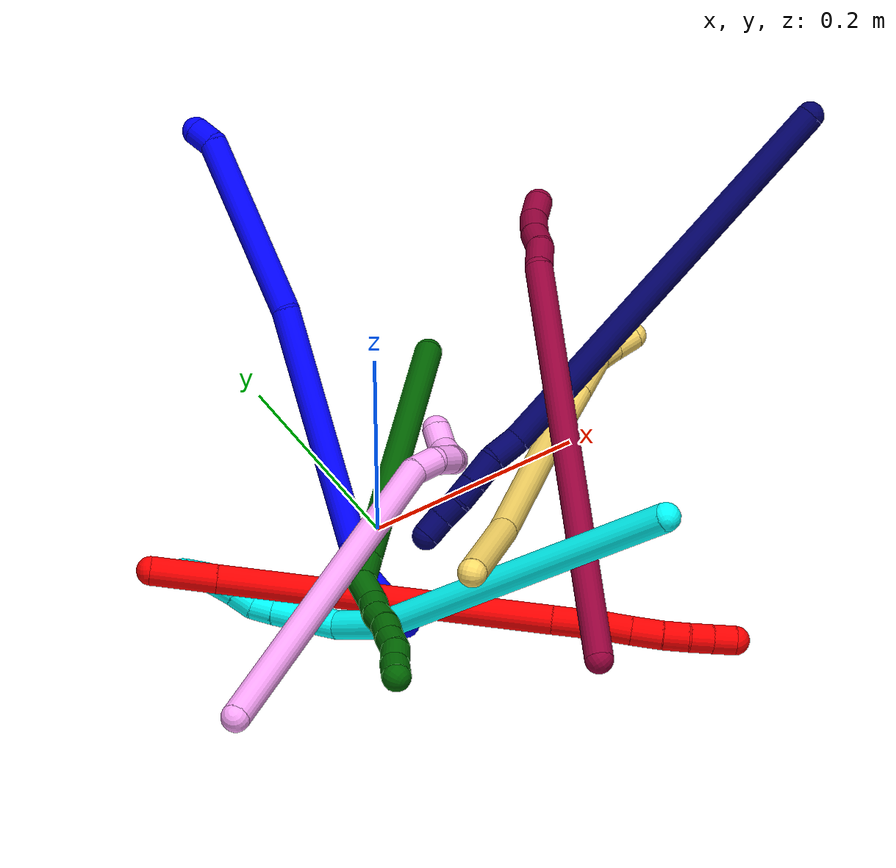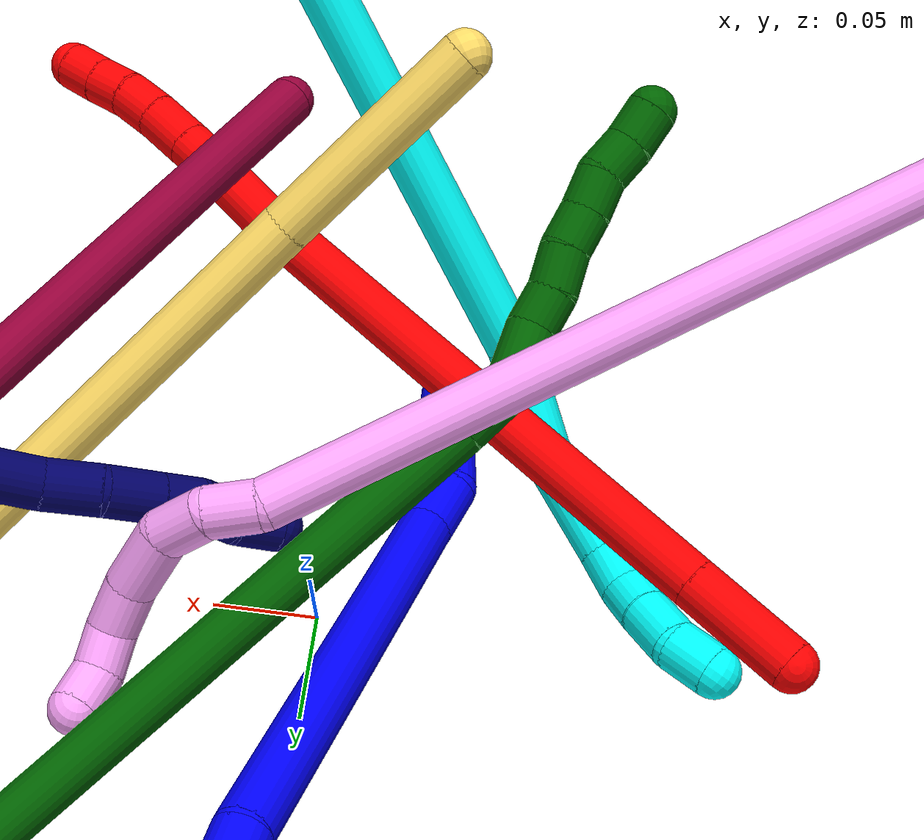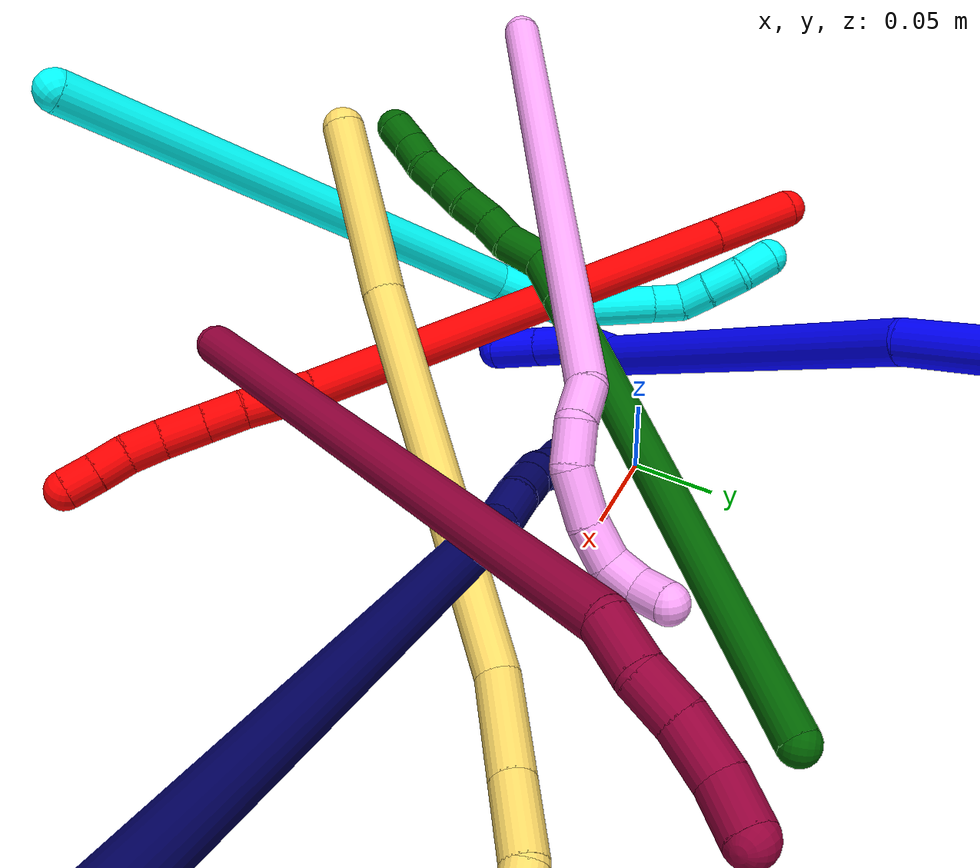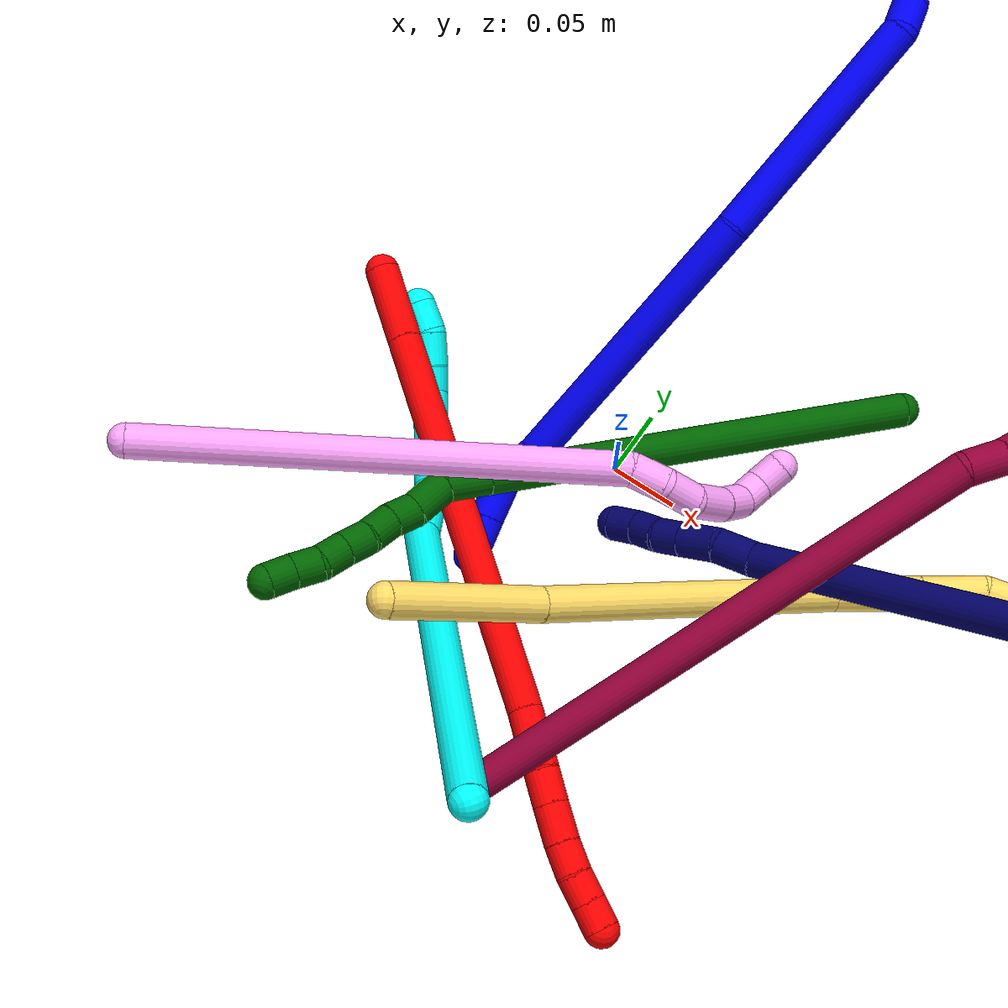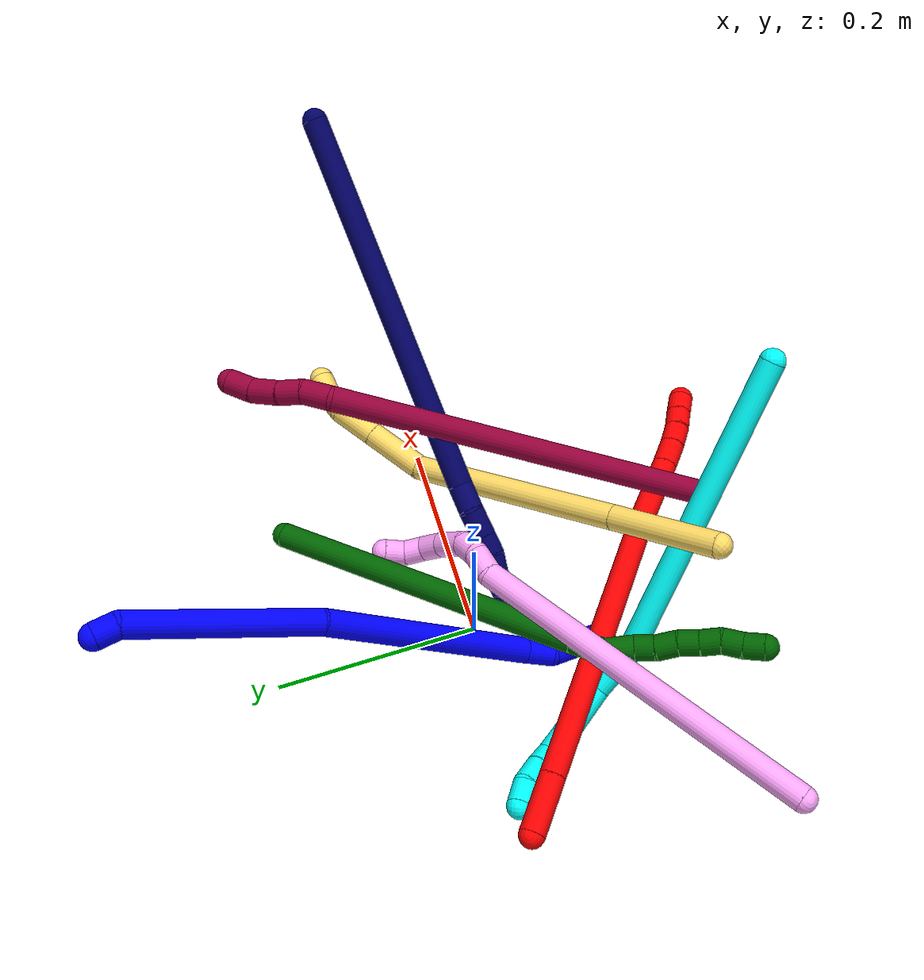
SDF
<sdf version="1.7">
 <world name="default">
  <plugin name="TubeGeneratorPlugin" filename="libtube_generator_plugin.so"/>
  <model name="photoneo_s_sensor">
   <static>1</static>
   <pose>0 0 2 1.57079 1.57079 3.14159</pose>
   <link name="link">
    <inertial><mass>0.1</mass></inertial>
    <sensor name="sensor" type="depth">
     <update_rate>30</update_rate>
     <camera>
      <horizontal_fov>1.22</horizontal_fov>
      <image><width>1920</width><height>1200</height><format>B8G8R8</format></image>
      <clip><near>0.1</near><far>4</far></clip>
      <depth_camera><output>points</output></depth_camera>
     </camera>
     <plugin name="camera_plugin" filename="libgazebo_ros_depth_camera.so">
      <baseline>0.2</baseline>
      <alwaysOn>1</alwaysOn>
      <updateRate>0.0</updateRate>
      <cameraName>camera_ir</cameraName>
      <imageTopicName>/camera/color/image_raw</imageTopicName>
      <cameraInfoTopicName>/camera/color/camera_info</cameraInfoTopicName>
      <depthImageTopicName>/camera/depth/image_raw</depthImageTopicName>
      <depthImageCameraInfoTopicName>/camera/depth/camera_info</depthImageCameraInfoTopicName>
      <pointCloudTopicName>/camera/depth/points</pointCloudTopicName>
      <frameName>fr_optical</frameName>
      <pointCloudCutoff>0.1</pointCloudCutoff>
      <pointCloudCutoffMax>2.0</pointCloudCutoffMax>
      <distortionK1>0</distortionK1>
      <distortionK2>0</distortionK2>
      <distortionK3>0</distortionK3>
      <distortionT1>0</distortionT1>
      <distortionT2>0</distortionT2>
      <CxPrime>0</CxPrime>
      <Cx>0</Cx>
      <Cy>0</Cy>
      <focalLength>0</focalLength>
      <hackBaseline>0</hackBaseline>
     </plugin>
    </sensor>
   </link>
  </model>
  <gravity>0 0 -9.8</gravity>
  <magnetic_field>6e-06 2.3e-05 -4.2e-05</magnetic_field>
  <atmosphere type="adiabatic"/>
  <physics name="default_physics" default="0" type="ode">
   <max_step_size>0.003</max_step_size>
   <real_time_factor>1</real_time_factor>
   <real_time_update_rate>1000</real_time_update_rate>
   <max_contacts>10000</max_contacts>
   <ode>
    <solver>
     <type>quick</type>
     <iters>100</iters>
     <sor>1.3</sor>
     <use_dynamic_moi_rescaling>0</use_dynamic_moi_rescaling>
    </solver>
    <constraints>
     <contact_max_correcting_vel>0</contact_max_correcting_vel>
     <contact_surface_layer>0.001</contact_surface_layer>
     <cfm>0</cfm>
     <erp>0.2</erp>
    </constraints>
   </ode>
  </physics>
  <scene><ambient>0.4 0.4 0.4 1</ambient><background>0.7 0.7 0.7 1</background><shadows>0</shadows></scene>
  <audio><device>default</device></audio>
  <spherical_coordinates>
   <surface_model>EARTH_WGS84</surface_model>
   <latitude_deg>0</latitude_deg>
   <longitude_deg>0</longitude_deg>
   <elevation>0</elevation>
   <heading_deg>0</heading_deg>
  </spherical_coordinates>
  <model name="bin">
   <static>1</static>
   <link name="bottom">
    <collision name="collision-bottom">
     <pose>0 0 -0.01 0 -0 0</pose>
     <geometry><box><size>0.8 0.6 0.02</size></box></geometry>
     <surface>
      <friction><ode><mu>100</mu><mu2>100</mu2></ode></friction>
      <contact><collide_bitmask>65535</collide_bitmask></contact>
     </surface>
    </collision>
   </link>
   <link name="west_wall">
    <collision name="collision-west_wall">
     <pose>-0.41 0 0.1 0 -0 0</pose>
     <geometry><box><size>0.02 0.6 0.2</size></box></geometry>
     <surface>
      <friction><ode><mu>100</mu><mu2>100</mu2></ode></friction>
      <contact><collide_bitmask>65535</collide_bitmask></contact>
     </surface>
    </collision>
   </link>
   <link name="east_wall">
    <collision name="collision-east_wall">
     <pose>0.41 0 0.1 0 -0 0</pose>
     <geometry><box><size>0.02 0.6 0.2</size></box></geometry>
     <surface>
      <friction><ode><mu>100</mu><mu2>100</mu2></ode></friction>
      <contact><collide_bitmask>65535</collide_bitmask></contact>
     </surface>
    </collision>
   </link>
   <link name="south_wall">
    <collision name="collision-south_wall">
     <pose>0 -0.31 0.1 0 -0 0</pose>
     <geometry><box><size>0.8 0.02 0.2</size></box></geometry>
     <surface>
      <friction><ode><mu>100</mu><mu2>100</mu2></ode></friction>
      <contact><collide_bitmask>65535</collide_bitmask></contact>
     </surface>
    </collision>
   </link>
   <link name="north_wall">
    <collision name="collision-north_wall">
     <pose>0 0.31 0.1 0 -0 0</pose>
     <geometry><box><size>0.8 0.02 0.2</size></box></geometry>
     <surface>
      <friction><ode><mu>100</mu><mu2>100</mu2></ode></friction>
      <contact><collide_bitmask>65535</collide_bitmask></contact>
     </surface>
    </collision>
   </link>
  </model>
  <model name="1">
   <static>0</static>
   <link name="1">
    <collision name="collision-cylinder-e_1_1_4">
     <pose>-0.005863 -0.007229 -0.005889 2.25435 -0.561339 -1.09056</pose>
     <geometry><cylinder><radius>0.0125</radius><length>0.022029</length></cylinder></geometry>
     <surface>
      <friction><ode><mu>1.16</mu><mu2>1.16</mu2><slip1>0</slip1><slip2>0</slip2></ode></friction>
      <contact><ode><kp>1e+06</kp><kd>1</kd><max_vel>0</max_vel><min_depth>0.001</min_depth></ode></contact>
     </surface>
    </collision>
    <visual name="visual-cylinder-e_1_1_4">
     <pose>-0.005863 -0.007229 -0.005889 2.25435 -0.561339 -1.09056</pose>
     <geometry><cylinder><radius>0.0125</radius><length>0.022029</length></cylinder></geometry>
     <material><ambient>0 0 1 1</ambient></material>
    </visual>
    <collision name="collision-cylinder-e_2_4_5">
     <pose>-0.0304 -0.094036 -0.043164 1.94648 -0.214925 -0.314412</pose>
     <geometry><cylinder><radius>0.0125</radius><length>0.175115</length></cylinder></geometry>
     <surface>
      <friction><ode><mu>1.16</mu><mu2>1.16</mu2><slip1>0</slip1><slip2>0</slip2></ode></friction>
      <contact><ode><kp>1e+06</kp><kd>1</kd><max_vel>0</max_vel><min_depth>0.001</min_depth></ode></contact>
     </surface>
    </collision>
    <visual name="visual-cylinder-e_2_4_5">
     <pose>-0.0304 -0.094036 -0.043164 1.94648 -0.214925 -0.314412</pose>
     <geometry><cylinder><radius>0.0125</radius><length>0.175115</length></cylinder></geometry>
     <material><ambient>0 0 1 1</ambient></material>
    </visual>
    <collision name="collision-cylinder-e_3_5_6">
     <pose>-0.066142 -0.277912 -0.091804 1.73474 -0.16007 -0.18857</pose>
     <geometry><cylinder><radius>0.0125</radius><length>0.214171</length></cylinder></geometry>
     <surface>
      <friction><ode><mu>1.16</mu><mu2>1.16</mu2><slip1>0</slip1><slip2>0</slip2></ode></friction>
      <contact><ode><kp>1e+06</kp><kd>1</kd><max_vel>0</max_vel><min_depth>0.001</min_depth></ode></contact>
     </surface>
    </collision>
    <visual name="visual-cylinder-e_3_5_6">
     <pose>-0.066142 -0.277912 -0.091804 1.73474 -0.16007 -0.18857</pose>
     <geometry><cylinder><radius>0.0125</radius><length>0.214171</length></cylinder></geometry>
     <material><ambient>0 0 1 1</ambient></material>
    </visual>
    <collision name="collision-cylinder-e_4_6_7">
     <pose>-0.083749 -0.394369 -0.115076 2.0304 -0.039717 -0.063961</pose>
     <geometry><cylinder><radius>0.0125</radius><length>0.027154</length></cylinder></geometry>
     <surface>
      <friction><ode><mu>1.16</mu><mu2>1.16</mu2><slip1>0</slip1><slip2>0</slip2></ode></friction>
      <contact><ode><kp>1e+06</kp><kd>1</kd><max_vel>0</max_vel><min_depth>0.001</min_depth></ode></contact>
     </surface>
    </collision>
    <visual name="visual-cylinder-e_4_6_7">
     <pose>-0.083749 -0.394369 -0.115076 2.0304 -0.039717 -0.063961</pose>
     <geometry><cylinder><radius>0.0125</radius><length>0.027154</length></cylinder></geometry>
     <material><ambient>0 0 1 1</ambient></material>
    </visual>
    <collision name="collision-cylinder-e_5_7_8">
     <pose>-0.091835 -0.419054 -0.126596 1.98468 -0.504066 -0.751284</pose>
     <geometry><cylinder><radius>0.0125</radius><length>0.03125</length></cylinder></geometry>
     <surface>
      <friction><ode><mu>1.16</mu><mu2>1.16</mu2><slip1>0</slip1><slip2>0</slip2></ode></friction>
      <contact><ode><kp>1e+06</kp><kd>1</kd><max_vel>0</max_vel><min_depth>0.001</min_depth></ode></contact>
     </surface>
    </collision>
    <visual name="visual-cylinder-e_5_7_8">
     <pose>-0.091835 -0.419054 -0.126596 1.98468 -0.504066 -0.751284</pose>
     <geometry><cylinder><radius>0.0125</radius><length>0.03125</length></cylinder></geometry>
     <material><ambient>0 0 1 1</ambient></material>
    </visual>
    <collision name="collision-cylinder-e_6_8_2">
     <pose>-0.107004 -0.443444 -0.137612 2.00585 -0.527615 -0.800992</pose>
     <geometry><cylinder><radius>0.0125</radius><length>0.030282</length></cylinder></geometry>
     <surface>
      <friction><ode><mu>1.16</mu><mu2>1.16</mu2><slip1>0</slip1><slip2>0</slip2></ode></friction>
      <contact><ode><kp>1e+06</kp><kd>1</kd><max_vel>0</max_vel><min_depth>0.001</min_depth></ode></contact>
     </surface>
    </collision>
    <visual name="visual-cylinder-e_6_8_2">
     <pose>-0.107004 -0.443444 -0.137612 2.00585 -0.527615 -0.800992</pose>
     <geometry><cylinder><radius>0.0125</radius><length>0.030282</length></cylinder></geometry>
     <material><ambient>0 0 1 1</ambient></material>
    </visual>
    <collision name="collision-sphere-2">
     <pose>-0.114627 -0.455307 -0.143126 0 -0 0</pose>
     <geometry><sphere><radius>0.0125</radius></sphere></geometry>
     <surface>
      <friction><ode><mu>1.16</mu><mu2>1.16</mu2><slip1>0</slip1><slip2>0</slip2></ode></friction>
      <contact><ode><kp>1e+06</kp><kd>1</kd><max_vel>0</max_vel><min_depth>0.001</min_depth></ode></contact>
     </surface>
    </collision>
    <visual name="visual-sphere-2">
     <pose>-0.114627 -0.455307 -0.143126 0 -0 0</pose>
     <geometry><sphere><radius>0.0125</radius></sphere></geometry>
     <material><ambient>0 0 1 1</ambient></material>
    </visual>
    <collision name="collision-sphere-4">
     <pose>-0.011726 -0.014459 -0.011777 0 -0 0</pose>
     <geometry><sphere><radius>0.0125</radius></sphere></geometry>
     <surface>
      <friction><ode><mu>1.16</mu><mu2>1.16</mu2><slip1>0</slip1><slip2>0</slip2></ode></friction>
      <contact><ode><kp>1e+06</kp><kd>1</kd><max_vel>0</max_vel><min_depth>0.001</min_depth></ode></contact>
     </surface>
    </collision>
    <visual name="visual-sphere-4">
     <pose>-0.011726 -0.014459 -0.011777 0 -0 0</pose>
     <geometry><sphere><radius>0.0125</radius></sphere></geometry>
     <material><ambient>0 0 1 1</ambient></material>
    </visual>
    <collision name="collision-sphere-1">
     <geometry><sphere><radius>0.0125</radius></sphere></geometry>
     <surface>
      <friction><ode><mu>1.16</mu><mu2>1.16</mu2><slip1>0</slip1><slip2>0</slip2></ode></friction>
      <contact><ode><kp>1e+06</kp><kd>1</kd><max_vel>0</max_vel><min_depth>0.001</min_depth></ode></contact>
     </surface>
    </collision>
    <visual name="visual-sphere-1">
     <geometry><sphere><radius>0.0125</radius></sphere></geometry>
     <material><ambient>0 0 1 1</ambient></material>
    </visual>
    <collision name="collision-sphere-8">
     <pose>-0.099381 -0.43158 -0.132099 0 -0 0</pose>
     <geometry><sphere><radius>0.0125</radius></sphere></geometry>
     <surface>
      <friction><ode><mu>1.16</mu><mu2>1.16</mu2><slip1>0</slip1><slip2>0</slip2></ode></friction>
      <contact><ode><kp>1e+06</kp><kd>1</kd><max_vel>0</max_vel><min_depth>0.001</min_depth></ode></contact>
     </surface>
    </collision>
    <visual name="visual-sphere-8">
     <pose>-0.099381 -0.43158 -0.132099 0 -0 0</pose>
     <geometry><sphere><radius>0.0125</radius></sphere></geometry>
     <material><ambient>0 0 1 1</ambient></material>
    </visual>
    <collision name="collision-sphere-5">
     <pose>-0.049074 -0.173613 -0.07455 0 -0 0</pose>
     <geometry><sphere><radius>0.0125</radius></sphere></geometry>
     <surface>
      <friction><ode><mu>1.16</mu><mu2>1.16</mu2><slip1>0</slip1><slip2>0</slip2></ode></friction>
      <contact><ode><kp>1e+06</kp><kd>1</kd><max_vel>0</max_vel><min_depth>0.001</min_depth></ode></contact>
     </surface>
    </collision>
    <visual name="visual-sphere-5">
     <pose>-0.049074 -0.173613 -0.07455 0 -0 0</pose>
     <geometry><sphere><radius>0.0125</radius></sphere></geometry>
     <material><ambient>0 0 1 1</ambient></material>
    </visual>
    <collision name="collision-sphere-6">
     <pose>-0.08321 -0.382211 -0.109058 0 -0 0</pose>
     <geometry><sphere><radius>0.0125</radius></sphere></geometry>
     <surface>
      <friction><ode><mu>1.16</mu><mu2>1.16</mu2><slip1>0</slip1><slip2>0</slip2></ode></friction>
      <contact><ode><kp>1e+06</kp><kd>1</kd><max_vel>0</max_vel><min_depth>0.001</min_depth></ode></contact>
     </surface>
    </collision>
    <visual name="visual-sphere-6">
     <pose>-0.08321 -0.382211 -0.109058 0 -0 0</pose>
     <geometry><sphere><radius>0.0125</radius></sphere></geometry>
     <material><ambient>0 0 1 1</ambient></material>
    </visual>
    <collision name="collision-sphere-7">
     <pose>-0.084288 -0.406528 -0.121094 0 -0 0</pose>
     <geometry><sphere><radius>0.0125</radius></sphere></geometry>
     <surface>
      <friction><ode><mu>1.16</mu><mu2>1.16</mu2><slip1>0</slip1><slip2>0</slip2></ode></friction>
      <contact><ode><kp>1e+06</kp><kd>1</kd><max_vel>0</max_vel><min_depth>0.001</min_depth></ode></contact>
     </surface>
    </collision>
    <visual name="visual-sphere-7">
     <pose>-0.084288 -0.406528 -0.121094 0 -0 0</pose>
     <geometry><sphere><radius>0.0125</radius></sphere></geometry>
     <material><ambient>0 0 1 1</ambient></material>
    </visual>
    <inertial>
     <pose>-0.056005 -0.226758 -0.077196 0 -0 0</pose>
     <mass>0.5</mass>
     <inertia>
      <ixx>0.000927</ixx>
      <ixy>0</ixy>
      <ixz>0</ixz>
      <iyy>-0.000572</iyy>
      <iyz>0</iyz>
      <izz>0.00145</izz>
     </inertia>
    </inertial>
   </link>
   <pose>0.016631 0.323028 0.215282 2.43262 -0.161701 2.81336</pose>
  </model>
  <model name="2">
   <static>0</static>
   <link name="2">
    <collision name="collision-cylinder-e_1_1_4">
     <pose>0.008314 -0.025515 -0.009851 1.93926 0.295114 0.42684</pose>
     <geometry><cylinder><radius>0.0125</radius><length>0.057173</length></cylinder></geometry>
     <surface>
      <friction><ode><mu>1.16</mu><mu2>1.16</mu2><slip1>0</slip1><slip2>0</slip2></ode></friction>
      <contact><ode><kp>1e+06</kp><kd>1</kd><max_vel>0</max_vel><min_depth>0.001</min_depth></ode></contact>
     </surface>
    </collision>
    <visual name="visual-cylinder-e_1_1_4">
     <pose>0.008314 -0.025515 -0.009851 1.93926 0.295114 0.42684</pose>
     <geometry><cylinder><radius>0.0125</radius><length>0.057173</length></cylinder></geometry>
     <material><ambient>1 0 0 1</ambient></material>
    </visual>
    <collision name="collision-cylinder-e_2_4_5">
     <pose>0.058267 -0.178654 -0.068779 1.9379 0.295597 0.426923</pose>
     <geometry><cylinder><radius>0.0125</radius><length>0.285868</length></cylinder></geometry>
     <surface>
      <friction><ode><mu>1.16</mu><mu2>1.16</mu2><slip1>0</slip1><slip2>0</slip2></ode></friction>
      <contact><ode><kp>1e+06</kp><kd>1</kd><max_vel>0</max_vel><min_depth>0.001</min_depth></ode></contact>
     </surface>
    </collision>
    <visual name="visual-cylinder-e_2_4_5">
     <pose>0.058267 -0.178654 -0.068779 1.9379 0.295597 0.426923</pose>
     <geometry><cylinder><radius>0.0125</radius><length>0.285868</length></cylinder></geometry>
     <material><ambient>1 0 0 1</ambient></material>
    </visual>
    <collision name="collision-cylinder-e_3_5_6">
     <pose>0.10487 -0.326383 -0.124118 1.87278 0.231535 0.313454</pose>
     <geometry><cylinder><radius>0.0125</radius><length>0.043271</length></cylinder></geometry>
     <surface>
      <friction><ode><mu>1.16</mu><mu2>1.16</mu2><slip1>0</slip1><slip2>0</slip2></ode></friction>
      <contact><ode><kp>1e+06</kp><kd>1</kd><max_vel>0</max_vel><min_depth>0.001</min_depth></ode></contact>
     </surface>
    </collision>
    <visual name="visual-cylinder-e_3_5_6">
     <pose>0.10487 -0.326383 -0.124118 1.87278 0.231535 0.313454</pose>
     <geometry><cylinder><radius>0.0125</radius><length>0.043271</length></cylinder></geometry>
     <material><ambient>1 0 0 1</ambient></material>
    </visual>
    <collision name="collision-cylinder-e_4_6_7">
     <pose>0.112873 -0.357294 -0.134946 1.97052 0.253418 0.379598</pose>
     <geometry><cylinder><radius>0.0125</radius><length>0.024235</length></cylinder></geometry>
     <surface>
      <friction><ode><mu>1.16</mu><mu2>1.16</mu2><slip1>0</slip1><slip2>0</slip2></ode></friction>
      <contact><ode><kp>1e+06</kp><kd>1</kd><max_vel>0</max_vel><min_depth>0.001</min_depth></ode></contact>
     </surface>
    </collision>
    <visual name="visual-cylinder-e_4_6_7">
     <pose>0.112873 -0.357294 -0.134946 1.97052 0.253418 0.379598</pose>
     <geometry><cylinder><radius>0.0125</radius><length>0.024235</length></cylinder></geometry>
     <material><ambient>1 0 0 1</ambient></material>
    </visual>
    <collision name="collision-cylinder-e_5_7_8">
     <pose>0.119526 -0.380234 -0.144345 1.9499 0.270066 0.395495</pose>
     <geometry><cylinder><radius>0.0125</radius><length>0.027105</length></cylinder></geometry>
     <surface>
      <friction><ode><mu>1.16</mu><mu2>1.16</mu2><slip1>0</slip1><slip2>0</slip2></ode></friction>
      <contact><ode><kp>1e+06</kp><kd>1</kd><max_vel>0</max_vel><min_depth>0.001</min_depth></ode></contact>
     </surface>
    </collision>
    <visual name="visual-cylinder-e_5_7_8">
     <pose>0.119526 -0.380234 -0.144345 1.9499 0.270066 0.395495</pose>
     <geometry><cylinder><radius>0.0125</radius><length>0.027105</length></cylinder></geometry>
     <material><ambient>1 0 0 1</ambient></material>
    </visual>
    <collision name="collision-cylinder-e_6_8_9">
     <pose>0.126879 -0.402078 -0.152884 1.93539 0.345172 0.495819</pose>
     <geometry><cylinder><radius>0.0125</radius><length>0.022089</length></cylinder></geometry>
     <surface>
      <friction><ode><mu>1.16</mu><mu2>1.16</mu2><slip1>0</slip1><slip2>0</slip2></ode></friction>
      <contact><ode><kp>1e+06</kp><kd>1</kd><max_vel>0</max_vel><min_depth>0.001</min_depth></ode></contact>
     </surface>
    </collision>
    <visual name="visual-cylinder-e_6_8_9">
     <pose>0.126879 -0.402078 -0.152884 1.93539 0.345172 0.495819</pose>
     <geometry><cylinder><radius>0.0125</radius><length>0.022089</length></cylinder></geometry>
     <material><ambient>1 0 0 1</ambient></material>
    </visual>
    <collision name="collision-cylinder-e_7_9_10">
     <pose>0.135239 -0.419877 -0.160529 2.02386 0.474648 0.738121</pose>
     <geometry><cylinder><radius>0.0125</radius><length>0.020232</length></cylinder></geometry>
     <surface>
      <friction><ode><mu>1.16</mu><mu2>1.16</mu2><slip1>0</slip1><slip2>0</slip2></ode></friction>
      <contact><ode><kp>1e+06</kp><kd>1</kd><max_vel>0</max_vel><min_depth>0.001</min_depth></ode></contact>
     </surface>
    </collision>
    <visual name="visual-cylinder-e_7_9_10">
     <pose>0.135239 -0.419877 -0.160529 2.02386 0.474648 0.738121</pose>
     <geometry><cylinder><radius>0.0125</radius><length>0.020232</length></cylinder></geometry>
     <material><ambient>1 0 0 1</ambient></material>
    </visual>
    <collision name="collision-cylinder-e_8_10_2">
     <pose>0.144195 -0.436216 -0.168136 1.98931 0.447463 0.673778</pose>
     <geometry><cylinder><radius>0.0125</radius><length>0.020027</length></cylinder></geometry>
     <surface>
      <friction><ode><mu>1.16</mu><mu2>1.16</mu2><slip1>0</slip1><slip2>0</slip2></ode></friction>
      <contact><ode><kp>1e+06</kp><kd>1</kd><max_vel>0</max_vel><min_depth>0.001</min_depth></ode></contact>
     </surface>
    </collision>
    <visual name="visual-cylinder-e_8_10_2">
     <pose>0.144195 -0.436216 -0.168136 1.98931 0.447463 0.673778</pose>
     <geometry><cylinder><radius>0.0125</radius><length>0.020027</length></cylinder></geometry>
     <material><ambient>1 0 0 1</ambient></material>
    </visual>
    <collision name="collision-sphere-2">
     <pose>0.148528 -0.444465 -0.171805 0 -0 0</pose>
     <geometry><sphere><radius>0.0125</radius></sphere></geometry>
     <surface>
      <friction><ode><mu>1.16</mu><mu2>1.16</mu2><slip1>0</slip1><slip2>0</slip2></ode></friction>
      <contact><ode><kp>1e+06</kp><kd>1</kd><max_vel>0</max_vel><min_depth>0.001</min_depth></ode></contact>
     </surface>
    </collision>
    <visual name="visual-sphere-2">
     <pose>0.148528 -0.444465 -0.171805 0 -0 0</pose>
     <geometry><sphere><radius>0.0125</radius></sphere></geometry>
     <material><ambient>1 0 0 1</ambient></material>
    </visual>
    <collision name="collision-sphere-10">
     <pose>0.139863 -0.427967 -0.164467 0 -0 0</pose>
     <geometry><sphere><radius>0.0125</radius></sphere></geometry>
     <surface>
      <friction><ode><mu>1.16</mu><mu2>1.16</mu2><slip1>0</slip1><slip2>0</slip2></ode></friction>
      <contact><ode><kp>1e+06</kp><kd>1</kd><max_vel>0</max_vel><min_depth>0.001</min_depth></ode></contact>
     </surface>
    </collision>
    <visual name="visual-sphere-10">
     <pose>0.139863 -0.427967 -0.164467 0 -0 0</pose>
     <geometry><sphere><radius>0.0125</radius></sphere></geometry>
     <material><ambient>1 0 0 1</ambient></material>
    </visual>
    <collision name="collision-sphere-9">
     <pose>0.130616 -0.411788 -0.15659 0 -0 0</pose>
     <geometry><sphere><radius>0.0125</radius></sphere></geometry>
     <surface>
      <friction><ode><mu>1.16</mu><mu2>1.16</mu2><slip1>0</slip1><slip2>0</slip2></ode></friction>
      <contact><ode><kp>1e+06</kp><kd>1</kd><max_vel>0</max_vel><min_depth>0.001</min_depth></ode></contact>
     </surface>
    </collision>
    <visual name="visual-sphere-9">
     <pose>0.130616 -0.411788 -0.15659 0 -0 0</pose>
     <geometry><sphere><radius>0.0125</radius></sphere></geometry>
     <material><ambient>1 0 0 1</ambient></material>
    </visual>
    <collision name="collision-sphere-4">
     <pose>0.016629 -0.05103 -0.019703 0 -0 0</pose>
     <geometry><sphere><radius>0.0125</radius></sphere></geometry>
     <surface>
      <friction><ode><mu>1.16</mu><mu2>1.16</mu2><slip1>0</slip1><slip2>0</slip2></ode></friction>
      <contact><ode><kp>1e+06</kp><kd>1</kd><max_vel>0</max_vel><min_depth>0.001</min_depth></ode></contact>
     </surface>
    </collision>
    <visual name="visual-sphere-4">
     <pose>0.016629 -0.05103 -0.019703 0 -0 0</pose>
     <geometry><sphere><radius>0.0125</radius></sphere></geometry>
     <material><ambient>1 0 0 1</ambient></material>
    </visual>
    <collision name="collision-sphere-1">
     <geometry><sphere><radius>0.0125</radius></sphere></geometry>
     <surface>
      <friction><ode><mu>1.16</mu><mu2>1.16</mu2><slip1>0</slip1><slip2>0</slip2></ode></friction>
      <contact><ode><kp>1e+06</kp><kd>1</kd><max_vel>0</max_vel><min_depth>0.001</min_depth></ode></contact>
     </surface>
    </collision>
    <visual name="visual-sphere-1">
     <geometry><sphere><radius>0.0125</radius></sphere></geometry>
     <material><ambient>1 0 0 1</ambient></material>
    </visual>
    <collision name="collision-sphere-8">
     <pose>0.123142 -0.392368 -0.149178 0 -0 0</pose>
     <geometry><sphere><radius>0.0125</radius></sphere></geometry>
     <surface>
      <friction><ode><mu>1.16</mu><mu2>1.16</mu2><slip1>0</slip1><slip2>0</slip2></ode></friction>
      <contact><ode><kp>1e+06</kp><kd>1</kd><max_vel>0</max_vel><min_depth>0.001</min_depth></ode></contact>
     </surface>
    </collision>
    <visual name="visual-sphere-8">
     <pose>0.123142 -0.392368 -0.149178 0 -0 0</pose>
     <geometry><sphere><radius>0.0125</radius></sphere></geometry>
     <material><ambient>1 0 0 1</ambient></material>
    </visual>
    <collision name="collision-sphere-5">
     <pose>0.099905 -0.306278 -0.117855 0 -0 0</pose>
     <geometry><sphere><radius>0.0125</radius></sphere></geometry>
     <surface>
      <friction><ode><mu>1.16</mu><mu2>1.16</mu2><slip1>0</slip1><slip2>0</slip2></ode></friction>
      <contact><ode><kp>1e+06</kp><kd>1</kd><max_vel>0</max_vel><min_depth>0.001</min_depth></ode></contact>
     </surface>
    </collision>
    <visual name="visual-sphere-5">
     <pose>0.099905 -0.306278 -0.117855 0 -0 0</pose>
     <geometry><sphere><radius>0.0125</radius></sphere></geometry>
     <material><ambient>1 0 0 1</ambient></material>
    </visual>
    <collision name="collision-sphere-6">
     <pose>0.109835 -0.346489 -0.130381 0 -0 0</pose>
     <geometry><sphere><radius>0.0125</radius></sphere></geometry>
     <surface>
      <friction><ode><mu>1.16</mu><mu2>1.16</mu2><slip1>0</slip1><slip2>0</slip2></ode></friction>
      <contact><ode><kp>1e+06</kp><kd>1</kd><max_vel>0</max_vel><min_depth>0.001</min_depth></ode></contact>
     </surface>
    </collision>
    <visual name="visual-sphere-6">
     <pose>0.109835 -0.346489 -0.130381 0 -0 0</pose>
     <geometry><sphere><radius>0.0125</radius></sphere></geometry>
     <material><ambient>1 0 0 1</ambient></material>
    </visual>
    <collision name="collision-sphere-7">
     <pose>0.115911 -0.3681 -0.139511 0 -0 0</pose>
     <geometry><sphere><radius>0.0125</radius></sphere></geometry>
     <surface>
      <friction><ode><mu>1.16</mu><mu2>1.16</mu2><slip1>0</slip1><slip2>0</slip2></ode></friction>
      <contact><ode><kp>1e+06</kp><kd>1</kd><max_vel>0</max_vel><min_depth>0.001</min_depth></ode></contact>
     </surface>
    </collision>
    <visual name="visual-sphere-7">
     <pose>0.115911 -0.3681 -0.139511 0 -0 0</pose>
     <geometry><sphere><radius>0.0125</radius></sphere></geometry>
     <material><ambient>1 0 0 1</ambient></material>
    </visual>
    <inertial>
     <pose>0.072143 -0.223462 -0.085541 0 -0 0</pose>
     <mass>0.5</mass>
     <inertia>
      <ixx>0.002537</ixx>
      <ixy>0</ixy>
      <ixz>0</ixz>
      <iyy>0.000328</iyy>
      <iyz>0</iyz>
      <izz>0.001186</izz>
     </inertia>
    </inertial>
   </link>
   <pose>-0.217229 0.013888 0.055869 -0.315361 0.122065 0.622601</pose>
  </model>
  <model name="3">
   <static>0</static>
   <link name="3">
    <collision name="collision-cylinder-e_1_1_4">
     <pose>-0.101077 0.094015 -0.061134 -2.14735 -0.733545 1.23219</pose>
     <geometry><cylinder><radius>0.0125</radius><length>0.301945</length></cylinder></geometry>
     <surface>
      <friction><ode><mu>1.16</mu><mu2>1.16</mu2><slip1>0</slip1><slip2>0</slip2></ode></friction>
      <contact><ode><kp>1e+06</kp><kd>1</kd><max_vel>0</max_vel><min_depth>0.001</min_depth></ode></contact>
     </surface>
    </collision>
    <visual name="visual-cylinder-e_1_1_4">
     <pose>-0.101077 0.094015 -0.061134 -2.14735 -0.733545 1.23219</pose>
     <geometry><cylinder><radius>0.0125</radius><length>0.301945</length></cylinder></geometry>
     <material><ambient>0.003922 1 0.996078 1</ambient></material>
    </visual>
    <collision name="collision-cylinder-e_2_4_5">
     <pose>-0.214316 0.205091 -0.13794 -2.31381 -0.483421 1.02285</pose>
     <geometry><cylinder><radius>0.0125</radius><length>0.052331</length></cylinder></geometry>
     <surface>
      <friction><ode><mu>1.16</mu><mu2>1.16</mu2><slip1>0</slip1><slip2>0</slip2></ode></friction>
      <contact><ode><kp>1e+06</kp><kd>1</kd><max_vel>0</max_vel><min_depth>0.001</min_depth></ode></contact>
     </surface>
    </collision>
    <visual name="visual-cylinder-e_2_4_5">
     <pose>-0.214316 0.205091 -0.13794 -2.31381 -0.483421 1.02285</pose>
     <geometry><cylinder><radius>0.0125</radius><length>0.052331</length></cylinder></geometry>
     <material><ambient>0.003922 1 0.996078 1</ambient></material>
    </visual>
    <collision name="collision-cylinder-e_3_5_6">
     <pose>-0.230747 0.248249 -0.16565 -2.00297 -0.147452 0.229796</pose>
     <geometry><cylinder><radius>0.0125</radius><length>0.05811</length></cylinder></geometry>
     <surface>
      <friction><ode><mu>1.16</mu><mu2>1.16</mu2><slip1>0</slip1><slip2>0</slip2></ode></friction>
      <contact><ode><kp>1e+06</kp><kd>1</kd><max_vel>0</max_vel><min_depth>0.001</min_depth></ode></contact>
     </surface>
    </collision>
    <visual name="visual-cylinder-e_3_5_6">
     <pose>-0.230747 0.248249 -0.16565 -2.00297 -0.147452 0.229796</pose>
     <geometry><cylinder><radius>0.0125</radius><length>0.05811</length></cylinder></geometry>
     <material><ambient>0.003922 1 0.996078 1</ambient></material>
    </visual>
    <collision name="collision-cylinder-e_4_6_7">
     <pose>-0.236142 0.283549 -0.182163 -2.0234 -0.109635 0.174951</pose>
     <geometry><cylinder><radius>0.0125</radius><length>0.020591</length></cylinder></geometry>
     <surface>
      <friction><ode><mu>1.16</mu><mu2>1.16</mu2><slip1>0</slip1><slip2>0</slip2></ode></friction>
      <contact><ode><kp>1e+06</kp><kd>1</kd><max_vel>0</max_vel><min_depth>0.001</min_depth></ode></contact>
     </surface>
    </collision>
    <visual name="visual-cylinder-e_4_6_7">
     <pose>-0.236142 0.283549 -0.182163 -2.0234 -0.109635 0.174951</pose>
     <geometry><cylinder><radius>0.0125</radius><length>0.020591</length></cylinder></geometry>
     <material><ambient>0.003922 1 0.996078 1</ambient></material>
    </visual>
    <collision name="collision-cylinder-e_5_7_8">
     <pose>-0.233642 0.301791 -0.18913 -1.83979 0.369091 -0.48071</pose>
     <geometry><cylinder><radius>0.0125</radius><length>0.020106</length></cylinder></geometry>
     <surface>
      <friction><ode><mu>1.16</mu><mu2>1.16</mu2><slip1>0</slip1><slip2>0</slip2></ode></friction>
      <contact><ode><kp>1e+06</kp><kd>1</kd><max_vel>0</max_vel><min_depth>0.001</min_depth></ode></contact>
     </surface>
    </collision>
    <visual name="visual-cylinder-e_5_7_8">
     <pose>-0.233642 0.301791 -0.18913 -1.83979 0.369091 -0.48071</pose>
     <geometry><cylinder><radius>0.0125</radius><length>0.020106</length></cylinder></geometry>
     <material><ambient>0.003922 1 0.996078 1</ambient></material>
    </visual>
    <collision name="collision-cylinder-e_6_8_9">
     <pose>-0.226397 0.322197 -0.194106 -1.78595 0.301431 -0.372898</pose>
     <geometry><cylinder><radius>0.0125</radius><length>0.024369</length></cylinder></geometry>
     <surface>
      <friction><ode><mu>1.16</mu><mu2>1.16</mu2><slip1>0</slip1><slip2>0</slip2></ode></friction>
      <contact><ode><kp>1e+06</kp><kd>1</kd><max_vel>0</max_vel><min_depth>0.001</min_depth></ode></contact>
     </surface>
    </collision>
    <visual name="visual-cylinder-e_6_8_9">
     <pose>-0.226397 0.322197 -0.194106 -1.78595 0.301431 -0.372898</pose>
     <geometry><cylinder><radius>0.0125</radius><length>0.024369</length></cylinder></geometry>
     <material><ambient>0.003922 1 0.996078 1</ambient></material>
    </visual>
    <collision name="collision-cylinder-e_7_9_2">
     <pose>-0.222437 0.344832 -0.196719 -1.58229 0.030392 -0.030743</pose>
     <geometry><cylinder><radius>0.0125</radius><length>0.022548</length></cylinder></geometry>
     <surface>
      <friction><ode><mu>1.16</mu><mu2>1.16</mu2><slip1>0</slip1><slip2>0</slip2></ode></friction>
      <contact><ode><kp>1e+06</kp><kd>1</kd><max_vel>0</max_vel><min_depth>0.001</min_depth></ode></contact>
     </surface>
    </collision>
    <visual name="visual-cylinder-e_7_9_2">
     <pose>-0.222437 0.344832 -0.196719 -1.58229 0.030392 -0.030743</pose>
     <geometry><cylinder><radius>0.0125</radius><length>0.022548</length></cylinder></geometry>
     <material><ambient>0.003922 1 0.996078 1</ambient></material>
    </visual>
    <collision name="collision-sphere-2">
     <pose>-0.222095 0.356101 -0.196849 0 -0 0</pose>
     <geometry><sphere><radius>0.0125</radius></sphere></geometry>
     <surface>
      <friction><ode><mu>1.16</mu><mu2>1.16</mu2><slip1>0</slip1><slip2>0</slip2></ode></friction>
      <contact><ode><kp>1e+06</kp><kd>1</kd><max_vel>0</max_vel><min_depth>0.001</min_depth></ode></contact>
     </surface>
    </collision>
    <visual name="visual-sphere-2">
     <pose>-0.222095 0.356101 -0.196849 0 -0 0</pose>
     <geometry><sphere><radius>0.0125</radius></sphere></geometry>
     <material><ambient>0.003922 1 0.996078 1</ambient></material>
    </visual>
    <collision name="collision-sphere-9">
     <pose>-0.22278 0.333564 -0.19659 0 -0 0</pose>
     <geometry><sphere><radius>0.0125</radius></sphere></geometry>
     <surface>
      <friction><ode><mu>1.16</mu><mu2>1.16</mu2><slip1>0</slip1><slip2>0</slip2></ode></friction>
      <contact><ode><kp>1e+06</kp><kd>1</kd><max_vel>0</max_vel><min_depth>0.001</min_depth></ode></contact>
     </surface>
    </collision>
    <visual name="visual-sphere-9">
     <pose>-0.22278 0.333564 -0.19659 0 -0 0</pose>
     <geometry><sphere><radius>0.0125</radius></sphere></geometry>
     <material><ambient>0.003922 1 0.996078 1</ambient></material>
    </visual>
    <collision name="collision-sphere-4">
     <pose>-0.202154 0.18803 -0.122267 0 -0 0</pose>
     <geometry><sphere><radius>0.0125</radius></sphere></geometry>
     <surface>
      <friction><ode><mu>1.16</mu><mu2>1.16</mu2><slip1>0</slip1><slip2>0</slip2></ode></friction>
      <contact><ode><kp>1e+06</kp><kd>1</kd><max_vel>0</max_vel><min_depth>0.001</min_depth></ode></contact>
     </surface>
    </collision>
    <visual name="visual-sphere-4">
     <pose>-0.202154 0.18803 -0.122267 0 -0 0</pose>
     <geometry><sphere><radius>0.0125</radius></sphere></geometry>
     <material><ambient>0.003922 1 0.996078 1</ambient></material>
    </visual>
    <collision name="collision-sphere-1">
     <geometry><sphere><radius>0.0125</radius></sphere></geometry>
     <surface>
      <friction><ode><mu>1.16</mu><mu2>1.16</mu2><slip1>0</slip1><slip2>0</slip2></ode></friction>
      <contact><ode><kp>1e+06</kp><kd>1</kd><max_vel>0</max_vel><min_depth>0.001</min_depth></ode></contact>
     </surface>
    </collision>
    <visual name="visual-sphere-1">
     <geometry><sphere><radius>0.0125</radius></sphere></geometry>
     <material><ambient>0.003922 1 0.996078 1</ambient></material>
    </visual>
    <collision name="collision-sphere-8">
     <pose>-0.230015 0.31083 -0.191622 0 -0 0</pose>
     <geometry><sphere><radius>0.0125</radius></sphere></geometry>
     <surface>
      <friction><ode><mu>1.16</mu><mu2>1.16</mu2><slip1>0</slip1><slip2>0</slip2></ode></friction>
      <contact><ode><kp>1e+06</kp><kd>1</kd><max_vel>0</max_vel><min_depth>0.001</min_depth></ode></contact>
     </surface>
    </collision>
    <visual name="visual-sphere-8">
     <pose>-0.230015 0.31083 -0.191622 0 -0 0</pose>
     <geometry><sphere><radius>0.0125</radius></sphere></geometry>
     <material><ambient>0.003922 1 0.996078 1</ambient></material>
    </visual>
    <collision name="collision-sphere-5">
     <pose>-0.226478 0.222152 -0.153613 0 -0 0</pose>
     <geometry><sphere><radius>0.0125</radius></sphere></geometry>
     <surface>
      <friction><ode><mu>1.16</mu><mu2>1.16</mu2><slip1>0</slip1><slip2>0</slip2></ode></friction>
      <contact><ode><kp>1e+06</kp><kd>1</kd><max_vel>0</max_vel><min_depth>0.001</min_depth></ode></contact>
     </surface>
    </collision>
    <visual name="visual-sphere-5">
     <pose>-0.226478 0.222152 -0.153613 0 -0 0</pose>
     <geometry><sphere><radius>0.0125</radius></sphere></geometry>
     <material><ambient>0.003922 1 0.996078 1</ambient></material>
    </visual>
    <collision name="collision-sphere-6">
     <pose>-0.235016 0.274346 -0.177687 0 -0 0</pose>
     <geometry><sphere><radius>0.0125</radius></sphere></geometry>
     <surface>
      <friction><ode><mu>1.16</mu><mu2>1.16</mu2><slip1>0</slip1><slip2>0</slip2></ode></friction>
      <contact><ode><kp>1e+06</kp><kd>1</kd><max_vel>0</max_vel><min_depth>0.001</min_depth></ode></contact>
     </surface>
    </collision>
    <visual name="visual-sphere-6">
     <pose>-0.235016 0.274346 -0.177687 0 -0 0</pose>
     <geometry><sphere><radius>0.0125</radius></sphere></geometry>
     <material><ambient>0.003922 1 0.996078 1</ambient></material>
    </visual>
    <collision name="collision-sphere-7">
     <pose>-0.237269 0.292753 -0.186638 0 -0 0</pose>
     <geometry><sphere><radius>0.0125</radius></sphere></geometry>
     <surface>
      <friction><ode><mu>1.16</mu><mu2>1.16</mu2><slip1>0</slip1><slip2>0</slip2></ode></friction>
      <contact><ode><kp>1e+06</kp><kd>1</kd><max_vel>0</max_vel><min_depth>0.001</min_depth></ode></contact>
     </surface>
    </collision>
    <visual name="visual-sphere-7">
     <pose>-0.237269 0.292753 -0.186638 0 -0 0</pose>
     <geometry><sphere><radius>0.0125</radius></sphere></geometry>
     <material><ambient>0.003922 1 0.996078 1</ambient></material>
    </visual>
    <inertial>
     <pose>-0.150473 0.162158 -0.104046 0 -0 0</pose>
     <mass>0.5</mass>
     <inertia>
      <ixx>0.002212</ixx>
      <ixy>0</ixy>
      <ixz>0</ixz>
      <iyy>0.002451</iyy>
      <iyz>0</iyz>
      <izz>6.8e-05</izz>
     </inertia>
    </inertial>
   </link>
   <pose>0.086142 -0.309185 0.226495 0.620953 -1.20568 0.402928</pose>
  </model>
  <model name="4">
   <static>0</static>
   <link name="4">
    <collision name="collision-cylinder-e_1_1_4">
     <pose>0.13562 0.074704 0.080033 -0.750976 0.891646 -0.372413</pose>
     <geometry><cylinder><radius>0.0125</radius><length>0.348589</length></cylinder></geometry>
     <surface>
      <friction><ode><mu>1.16</mu><mu2>1.16</mu2><slip1>0</slip1><slip2>0</slip2></ode></friction>
      <contact><ode><kp>1e+06</kp><kd>1</kd><max_vel>0</max_vel><min_depth>0.001</min_depth></ode></contact>
     </surface>
    </collision>
    <visual name="visual-cylinder-e_1_1_4">
     <pose>0.13562 0.074704 0.080033 -0.750976 0.891646 -0.372413</pose>
     <geometry><cylinder><radius>0.0125</radius><length>0.348589</length></cylinder></geometry>
     <material><ambient>1 0.65098 0.996078 1</ambient></material>
    </visual>
    <collision name="collision-cylinder-e_2_4_5">
     <pose>0.277809 0.158456 0.166396 -0.960266 0.536628 -0.284437</pose>
     <geometry><cylinder><radius>0.0125</radius><length>0.025698</length></cylinder></geometry>
     <surface>
      <friction><ode><mu>1.16</mu><mu2>1.16</mu2><slip1>0</slip1><slip2>0</slip2></ode></friction>
      <contact><ode><kp>1e+06</kp><kd>1</kd><max_vel>0</max_vel><min_depth>0.001</min_depth></ode></contact>
     </surface>
    </collision>
    <visual name="visual-cylinder-e_2_4_5">
     <pose>0.277809 0.158456 0.166396 -0.960266 0.536628 -0.284437</pose>
     <geometry><cylinder><radius>0.0125</radius><length>0.025698</length></cylinder></geometry>
     <material><ambient>1 0.65098 0.996078 1</ambient></material>
    </visual>
    <collision name="collision-cylinder-e_3_5_6">
     <pose>0.288992 0.173317 0.183292 -0.502955 0.365495 -0.09489</pose>
     <geometry><cylinder><radius>0.0125</radius><length>0.025823</length></cylinder></geometry>
     <surface>
      <friction><ode><mu>1.16</mu><mu2>1.16</mu2><slip1>0</slip1><slip2>0</slip2></ode></friction>
      <contact><ode><kp>1e+06</kp><kd>1</kd><max_vel>0</max_vel><min_depth>0.001</min_depth></ode></contact>
     </surface>
    </collision>
    <visual name="visual-cylinder-e_3_5_6">
     <pose>0.288992 0.173317 0.183292 -0.502955 0.365495 -0.09489</pose>
     <geometry><cylinder><radius>0.0125</radius><length>0.025823</length></cylinder></geometry>
     <material><ambient>1 0.65098 0.996078 1</ambient></material>
    </visual>
    <collision name="collision-cylinder-e_4_6_7">
     <pose>0.300106 0.179419 0.208887 -0.019255 0.408088 -0.003984</pose>
     <geometry><cylinder><radius>0.0125</radius><length>0.032753</length></cylinder></geometry>
     <surface>
      <friction><ode><mu>1.16</mu><mu2>1.16</mu2><slip1>0</slip1><slip2>0</slip2></ode></friction>
      <contact><ode><kp>1e+06</kp><kd>1</kd><max_vel>0</max_vel><min_depth>0.001</min_depth></ode></contact>
     </surface>
    </collision>
    <visual name="visual-cylinder-e_4_6_7">
     <pose>0.300106 0.179419 0.208887 -0.019255 0.408088 -0.003984</pose>
     <geometry><cylinder><radius>0.0125</radius><length>0.032753</length></cylinder></geometry>
     <material><ambient>1 0.65098 0.996078 1</ambient></material>
    </visual>
    <collision name="collision-cylinder-e_5_7_8">
     <pose>0.312455 0.177883 0.234518 0.170469 0.498017 0.043446</pose>
     <geometry><cylinder><radius>0.0125</radius><length>0.024491</length></cylinder></geometry>
     <surface>
      <friction><ode><mu>1.16</mu><mu2>1.16</mu2><slip1>0</slip1><slip2>0</slip2></ode></friction>
      <contact><ode><kp>1e+06</kp><kd>1</kd><max_vel>0</max_vel><min_depth>0.001</min_depth></ode></contact>
     </surface>
    </collision>
    <visual name="visual-cylinder-e_5_7_8">
     <pose>0.312455 0.177883 0.234518 0.170469 0.498017 0.043446</pose>
     <geometry><cylinder><radius>0.0125</radius><length>0.024491</length></cylinder></geometry>
     <material><ambient>1 0.65098 0.996078 1</ambient></material>
    </visual>
    <collision name="collision-cylinder-e_6_8_9">
     <pose>0.326394 0.172131 0.250862 0.599893 0.860565 0.28201</pose>
     <geometry><cylinder><radius>0.0125</radius><length>0.021337</length></cylinder></geometry>
     <surface>
      <friction><ode><mu>1.16</mu><mu2>1.16</mu2><slip1>0</slip1><slip2>0</slip2></ode></friction>
      <contact><ode><kp>1e+06</kp><kd>1</kd><max_vel>0</max_vel><min_depth>0.001</min_depth></ode></contact>
     </surface>
    </collision>
    <visual name="visual-cylinder-e_6_8_9">
     <pose>0.326394 0.172131 0.250862 0.599893 0.860565 0.28201</pose>
     <geometry><cylinder><radius>0.0125</radius><length>0.021337</length></cylinder></geometry>
     <material><ambient>1 0.65098 0.996078 1</ambient></material>
    </visual>
    <collision name="collision-cylinder-e_7_9_2">
     <pose>0.344878 0.166222 0.25783 1.01668 1.35024 0.839195</pose>
     <geometry><cylinder><radius>0.0125</radius><length>0.021307</length></cylinder></geometry>
     <surface>
      <friction><ode><mu>1.16</mu><mu2>1.16</mu2><slip1>0</slip1><slip2>0</slip2></ode></friction>
      <contact><ode><kp>1e+06</kp><kd>1</kd><max_vel>0</max_vel><min_depth>0.001</min_depth></ode></contact>
     </surface>
    </collision>
    <visual name="visual-cylinder-e_7_9_2">
     <pose>0.344878 0.166222 0.25783 1.01668 1.35024 0.839195</pose>
     <geometry><cylinder><radius>0.0125</radius><length>0.021307</length></cylinder></geometry>
     <material><ambient>1 0.65098 0.996078 1</ambient></material>
    </visual>
    <collision name="collision-sphere-2">
     <pose>0.355274 0.16424 0.259056 0 -0 0</pose>
     <geometry><sphere><radius>0.0125</radius></sphere></geometry>
     <surface>
      <friction><ode><mu>1.16</mu><mu2>1.16</mu2><slip1>0</slip1><slip2>0</slip2></ode></friction>
      <contact><ode><kp>1e+06</kp><kd>1</kd><max_vel>0</max_vel><min_depth>0.001</min_depth></ode></contact>
     </surface>
    </collision>
    <visual name="visual-sphere-2">
     <pose>0.355274 0.16424 0.259056 0 -0 0</pose>
     <geometry><sphere><radius>0.0125</radius></sphere></geometry>
     <material><ambient>1 0.65098 0.996078 1</ambient></material>
    </visual>
    <collision name="collision-sphere-9">
     <pose>0.334483 0.168204 0.256603 0 -0 0</pose>
     <geometry><sphere><radius>0.0125</radius></sphere></geometry>
     <surface>
      <friction><ode><mu>1.16</mu><mu2>1.16</mu2><slip1>0</slip1><slip2>0</slip2></ode></friction>
      <contact><ode><kp>1e+06</kp><kd>1</kd><max_vel>0</max_vel><min_depth>0.001</min_depth></ode></contact>
     </surface>
    </collision>
    <visual name="visual-sphere-9">
     <pose>0.334483 0.168204 0.256603 0 -0 0</pose>
     <geometry><sphere><radius>0.0125</radius></sphere></geometry>
     <material><ambient>1 0.65098 0.996078 1</ambient></material>
    </visual>
    <collision name="collision-sphere-4">
     <pose>0.27124 0.149408 0.160065 0 -0 0</pose>
     <geometry><sphere><radius>0.0125</radius></sphere></geometry>
     <surface>
      <friction><ode><mu>1.16</mu><mu2>1.16</mu2><slip1>0</slip1><slip2>0</slip2></ode></friction>
      <contact><ode><kp>1e+06</kp><kd>1</kd><max_vel>0</max_vel><min_depth>0.001</min_depth></ode></contact>
     </surface>
    </collision>
    <visual name="visual-sphere-4">
     <pose>0.27124 0.149408 0.160065 0 -0 0</pose>
     <geometry><sphere><radius>0.0125</radius></sphere></geometry>
     <material><ambient>1 0.65098 0.996078 1</ambient></material>
    </visual>
    <collision name="collision-sphere-1">
     <geometry><sphere><radius>0.0125</radius></sphere></geometry>
     <surface>
      <friction><ode><mu>1.16</mu><mu2>1.16</mu2><slip1>0</slip1><slip2>0</slip2></ode></friction>
      <contact><ode><kp>1e+06</kp><kd>1</kd><max_vel>0</max_vel><min_depth>0.001</min_depth></ode></contact>
     </surface>
    </collision>
    <visual name="visual-sphere-1">
     <geometry><sphere><radius>0.0125</radius></sphere></geometry>
     <material><ambient>1 0.65098 0.996078 1</ambient></material>
    </visual>
    <collision name="collision-sphere-8">
     <pose>0.318305 0.176058 0.24512 0 -0 0</pose>
     <geometry><sphere><radius>0.0125</radius></sphere></geometry>
     <surface>
      <friction><ode><mu>1.16</mu><mu2>1.16</mu2><slip1>0</slip1><slip2>0</slip2></ode></friction>
      <contact><ode><kp>1e+06</kp><kd>1</kd><max_vel>0</max_vel><min_depth>0.001</min_depth></ode></contact>
     </surface>
    </collision>
    <visual name="visual-sphere-8">
     <pose>0.318305 0.176058 0.24512 0 -0 0</pose>
     <geometry><sphere><radius>0.0125</radius></sphere></geometry>
     <material><ambient>1 0.65098 0.996078 1</ambient></material>
    </visual>
    <collision name="collision-sphere-5">
     <pose>0.284378 0.167504 0.172727 0 -0 0</pose>
     <geometry><sphere><radius>0.0125</radius></sphere></geometry>
     <surface>
      <friction><ode><mu>1.16</mu><mu2>1.16</mu2><slip1>0</slip1><slip2>0</slip2></ode></friction>
      <contact><ode><kp>1e+06</kp><kd>1</kd><max_vel>0</max_vel><min_depth>0.001</min_depth></ode></contact>
     </surface>
    </collision>
    <visual name="visual-sphere-5">
     <pose>0.284378 0.167504 0.172727 0 -0 0</pose>
     <geometry><sphere><radius>0.0125</radius></sphere></geometry>
     <material><ambient>1 0.65098 0.996078 1</ambient></material>
    </visual>
    <collision name="collision-sphere-6">
     <pose>0.293607 0.179129 0.193858 0 -0 0</pose>
     <geometry><sphere><radius>0.0125</radius></sphere></geometry>
     <surface>
      <friction><ode><mu>1.16</mu><mu2>1.16</mu2><slip1>0</slip1><slip2>0</slip2></ode></friction>
      <contact><ode><kp>1e+06</kp><kd>1</kd><max_vel>0</max_vel><min_depth>0.001</min_depth></ode></contact>
     </surface>
    </collision>
    <visual name="visual-sphere-6">
     <pose>0.293607 0.179129 0.193858 0 -0 0</pose>
     <geometry><sphere><radius>0.0125</radius></sphere></geometry>
     <material><ambient>1 0.65098 0.996078 1</ambient></material>
    </visual>
    <collision name="collision-sphere-7">
     <pose>0.306605 0.179708 0.223916 0 -0 0</pose>
     <geometry><sphere><radius>0.0125</radius></sphere></geometry>
     <surface>
      <friction><ode><mu>1.16</mu><mu2>1.16</mu2><slip1>0</slip1><slip2>0</slip2></ode></friction>
      <contact><ode><kp>1e+06</kp><kd>1</kd><max_vel>0</max_vel><min_depth>0.001</min_depth></ode></contact>
     </surface>
    </collision>
    <visual name="visual-sphere-7">
     <pose>0.306605 0.179708 0.223916 0 -0 0</pose>
     <geometry><sphere><radius>0.0125</radius></sphere></geometry>
     <material><ambient>1 0.65098 0.996078 1</ambient></material>
    </visual>
    <inertial>
     <pose>0.187344 0.104073 0.120679 0 -0 0</pose>
     <mass>0.5</mass>
     <inertia>
      <ixx>0.001302</ixx>
      <ixy>0</ixy>
      <ixz>0</ixz>
      <iyy>0.002313</iyy>
      <iyz>0</iyz>
      <izz>-0.004265</izz>
     </inertia>
    </inertial>
   </link>
   <pose>-0.266804 -0.213515 0.10822 2.98673 -0.357267 1.10084</pose>
  </model>
  <model name="5">
   <static>0</static>
   <link name="5">
    <collision name="collision-cylinder-e_1_1_4">
     <pose>0.051178 0.021163 -0.011749 -2.07761 1.12901 -1.64384</pose>
     <geometry><cylinder><radius>0.0125</radius><length>0.113227</length></cylinder></geometry>
     <surface>
      <friction><ode><mu>1.16</mu><mu2>1.16</mu2><slip1>0</slip1><slip2>0</slip2></ode></friction>
      <contact><ode><kp>1e+06</kp><kd>1</kd><max_vel>0</max_vel><min_depth>0.001</min_depth></ode></contact>
     </surface>
    </collision>
    <visual name="visual-cylinder-e_1_1_4">
     <pose>0.051178 0.021163 -0.011749 -2.07761 1.12901 -1.64384</pose>
     <geometry><cylinder><radius>0.0125</radius><length>0.113227</length></cylinder></geometry>
     <material><ambient>1 0.858824 0.4 1</ambient></material>
    </visual>
    <collision name="collision-cylinder-e_2_4_5">
     <pose>0.203442 0.091897 -0.051592 -2.0864 1.05752 -1.57347</pose>
     <geometry><cylinder><radius>0.0125</radius><length>0.232078</length></cylinder></geometry>
     <surface>
      <friction><ode><mu>1.16</mu><mu2>1.16</mu2><slip1>0</slip1><slip2>0</slip2></ode></friction>
      <contact><ode><kp>1e+06</kp><kd>1</kd><max_vel>0</max_vel><min_depth>0.001</min_depth></ode></contact>
     </surface>
    </collision>
    <visual name="visual-cylinder-e_2_4_5">
     <pose>0.203442 0.091897 -0.051592 -2.0864 1.05752 -1.57347</pose>
     <geometry><cylinder><radius>0.0125</radius><length>0.232078</length></cylinder></geometry>
     <material><ambient>1 0.858824 0.4 1</ambient></material>
    </visual>
    <collision name="collision-cylinder-e_3_5_6">
     <pose>0.324894 0.165232 -0.080473 -1.60391 0.70826 -0.730076</pose>
     <geometry><cylinder><radius>0.0125</radius><length>0.062613</length></cylinder></geometry>
     <surface>
      <friction><ode><mu>1.16</mu><mu2>1.16</mu2><slip1>0</slip1><slip2>0</slip2></ode></friction>
      <contact><ode><kp>1e+06</kp><kd>1</kd><max_vel>0</max_vel><min_depth>0.001</min_depth></ode></contact>
     </surface>
    </collision>
    <visual name="visual-cylinder-e_3_5_6">
     <pose>0.324894 0.165232 -0.080473 -1.60391 0.70826 -0.730076</pose>
     <geometry><cylinder><radius>0.0125</radius><length>0.062613</length></cylinder></geometry>
     <material><ambient>1 0.858824 0.4 1</ambient></material>
    </visual>
    <collision name="collision-cylinder-e_4_6_7">
     <pose>0.359893 0.20611 -0.081824 -1.60367 0.707198 -0.728831</pose>
     <geometry><cylinder><radius>0.0125</radius><length>0.04505</length></cylinder></geometry>
     <surface>
      <friction><ode><mu>1.16</mu><mu2>1.16</mu2><slip1>0</slip1><slip2>0</slip2></ode></friction>
      <contact><ode><kp>1e+06</kp><kd>1</kd><max_vel>0</max_vel><min_depth>0.001</min_depth></ode></contact>
     </surface>
    </collision>
    <visual name="visual-cylinder-e_4_6_7">
     <pose>0.359893 0.20611 -0.081824 -1.60367 0.707198 -0.728831</pose>
     <geometry><cylinder><radius>0.0125</radius><length>0.04505</length></cylinder></geometry>
     <material><ambient>1 0.858824 0.4 1</ambient></material>
    </visual>
    <collision name="collision-cylinder-e_5_7_8">
     <pose>0.383064 0.230194 -0.079511 -1.1796 0.84729 -0.586229</pose>
     <geometry><cylinder><radius>0.0125</radius><length>0.022779</length></cylinder></geometry>
     <surface>
      <friction><ode><mu>1.16</mu><mu2>1.16</mu2><slip1>0</slip1><slip2>0</slip2></ode></friction>
      <contact><ode><kp>1e+06</kp><kd>1</kd><max_vel>0</max_vel><min_depth>0.001</min_depth></ode></contact>
     </surface>
    </collision>
    <visual name="visual-cylinder-e_5_7_8">
     <pose>0.383064 0.230194 -0.079511 -1.1796 0.84729 -0.586229</pose>
     <geometry><cylinder><radius>0.0125</radius><length>0.022779</length></cylinder></geometry>
     <material><ambient>1 0.858824 0.4 1</ambient></material>
    </visual>
    <collision name="collision-cylinder-e_6_8_2">
     <pose>0.399012 0.245147 -0.071305 -0.981866 0.657478 -0.360749</pose>
     <geometry><cylinder><radius>0.0125</radius><length>0.024254</length></cylinder></geometry>
     <surface>
      <friction><ode><mu>1.16</mu><mu2>1.16</mu2><slip1>0</slip1><slip2>0</slip2></ode></friction>
      <contact><ode><kp>1e+06</kp><kd>1</kd><max_vel>0</max_vel><min_depth>0.001</min_depth></ode></contact>
     </surface>
    </collision>
    <visual name="visual-cylinder-e_6_8_2">
     <pose>0.399012 0.245147 -0.071305 -0.981866 0.657478 -0.360749</pose>
     <geometry><cylinder><radius>0.0125</radius><length>0.024254</length></cylinder></geometry>
     <material><ambient>1 0.858824 0.4 1</ambient></material>
    </visual>
    <collision name="collision-sphere-2">
     <pose>0.406423 0.253128 -0.065973 0 -0 0</pose>
     <geometry><sphere><radius>0.0125</radius></sphere></geometry>
     <surface>
      <friction><ode><mu>1.16</mu><mu2>1.16</mu2><slip1>0</slip1><slip2>0</slip2></ode></friction>
      <contact><ode><kp>1e+06</kp><kd>1</kd><max_vel>0</max_vel><min_depth>0.001</min_depth></ode></contact>
     </surface>
    </collision>
    <visual name="visual-sphere-2">
     <pose>0.406423 0.253128 -0.065973 0 -0 0</pose>
     <geometry><sphere><radius>0.0125</radius></sphere></geometry>
     <material><ambient>1 0.858824 0.4 1</ambient></material>
    </visual>
    <collision name="collision-sphere-4">
     <pose>0.102355 0.042325 -0.023498 0 -0 0</pose>
     <geometry><sphere><radius>0.0125</radius></sphere></geometry>
     <surface>
      <friction><ode><mu>1.16</mu><mu2>1.16</mu2><slip1>0</slip1><slip2>0</slip2></ode></friction>
      <contact><ode><kp>1e+06</kp><kd>1</kd><max_vel>0</max_vel><min_depth>0.001</min_depth></ode></contact>
     </surface>
    </collision>
    <visual name="visual-sphere-4">
     <pose>0.102355 0.042325 -0.023498 0 -0 0</pose>
     <geometry><sphere><radius>0.0125</radius></sphere></geometry>
     <material><ambient>1 0.858824 0.4 1</ambient></material>
    </visual>
    <collision name="collision-sphere-1">
     <geometry><sphere><radius>0.0125</radius></sphere></geometry>
     <surface>
      <friction><ode><mu>1.16</mu><mu2>1.16</mu2><slip1>0</slip1><slip2>0</slip2></ode></friction>
      <contact><ode><kp>1e+06</kp><kd>1</kd><max_vel>0</max_vel><min_depth>0.001</min_depth></ode></contact>
     </surface>
    </collision>
    <visual name="visual-sphere-1">
     <geometry><sphere><radius>0.0125</radius></sphere></geometry>
     <material><ambient>1 0.858824 0.4 1</ambient></material>
    </visual>
    <collision name="collision-sphere-8">
     <pose>0.3916 0.237165 -0.076637 0 -0 0</pose>
     <geometry><sphere><radius>0.0125</radius></sphere></geometry>
     <surface>
      <friction><ode><mu>1.16</mu><mu2>1.16</mu2><slip1>0</slip1><slip2>0</slip2></ode></friction>
      <contact><ode><kp>1e+06</kp><kd>1</kd><max_vel>0</max_vel><min_depth>0.001</min_depth></ode></contact>
     </surface>
    </collision>
    <visual name="visual-sphere-8">
     <pose>0.3916 0.237165 -0.076637 0 -0 0</pose>
     <geometry><sphere><radius>0.0125</radius></sphere></geometry>
     <material><ambient>1 0.858824 0.4 1</ambient></material>
    </visual>
    <collision name="collision-sphere-5">
     <pose>0.304529 0.141468 -0.079686 0 -0 0</pose>
     <geometry><sphere><radius>0.0125</radius></sphere></geometry>
     <surface>
      <friction><ode><mu>1.16</mu><mu2>1.16</mu2><slip1>0</slip1><slip2>0</slip2></ode></friction>
      <contact><ode><kp>1e+06</kp><kd>1</kd><max_vel>0</max_vel><min_depth>0.001</min_depth></ode></contact>
     </surface>
    </collision>
    <visual name="visual-sphere-5">
     <pose>0.304529 0.141468 -0.079686 0 -0 0</pose>
     <geometry><sphere><radius>0.0125</radius></sphere></geometry>
     <material><ambient>1 0.858824 0.4 1</ambient></material>
    </visual>
    <collision name="collision-sphere-6">
     <pose>0.345259 0.188996 -0.081261 0 -0 0</pose>
     <geometry><sphere><radius>0.0125</radius></sphere></geometry>
     <surface>
      <friction><ode><mu>1.16</mu><mu2>1.16</mu2><slip1>0</slip1><slip2>0</slip2></ode></friction>
      <contact><ode><kp>1e+06</kp><kd>1</kd><max_vel>0</max_vel><min_depth>0.001</min_depth></ode></contact>
     </surface>
    </collision>
    <visual name="visual-sphere-6">
     <pose>0.345259 0.188996 -0.081261 0 -0 0</pose>
     <geometry><sphere><radius>0.0125</radius></sphere></geometry>
     <material><ambient>1 0.858824 0.4 1</ambient></material>
    </visual>
    <collision name="collision-sphere-7">
     <pose>0.374528 0.223224 -0.082386 0 -0 0</pose>
     <geometry><sphere><radius>0.0125</radius></sphere></geometry>
     <surface>
      <friction><ode><mu>1.16</mu><mu2>1.16</mu2><slip1>0</slip1><slip2>0</slip2></ode></friction>
      <contact><ode><kp>1e+06</kp><kd>1</kd><max_vel>0</max_vel><min_depth>0.001</min_depth></ode></contact>
     </surface>
    </collision>
    <visual name="visual-sphere-7">
     <pose>0.374528 0.223224 -0.082386 0 -0 0</pose>
     <geometry><sphere><radius>0.0125</radius></sphere></geometry>
     <material><ambient>1 0.858824 0.4 1</ambient></material>
    </visual>
    <inertial>
     <pose>0.215936 0.109087 -0.051138 0 -0 0</pose>
     <mass>0.5</mass>
     <inertia>
      <ixx>-0.00054</ixx>
      <ixy>0</ixy>
      <ixz>0</ixz>
      <iyy>0.00035</iyy>
      <iyz>0</iyz>
      <izz>-0.00158</izz>
     </inertia>
    </inertial>
   </link>
   <pose>-0.041951 -0.21834 0.155553 1.38231 0.834026 0.437682</pose>
  </model>
  <model name="6">
   <static>0</static>
   <link name="6">
    <collision name="collision-cylinder-e_1_1_4">
     <pose>-0.125184 -0.044501 -0.086803 2.66786 -0.908861 -2.22372</pose>
     <geometry><cylinder><radius>0.0125</radius><length>0.317403</length></cylinder></geometry>
     <surface>
      <friction><ode><mu>1.16</mu><mu2>1.16</mu2><slip1>0</slip1><slip2>0</slip2></ode></friction>
      <contact><ode><kp>1e+06</kp><kd>1</kd><max_vel>0</max_vel><min_depth>0.001</min_depth></ode></contact>
     </surface>
    </collision>
    <visual name="visual-cylinder-e_1_1_4">
     <pose>-0.125184 -0.044501 -0.086803 2.66786 -0.908861 -2.22372</pose>
     <geometry><cylinder><radius>0.0125</radius><length>0.317403</length></cylinder></geometry>
     <material><ambient>0 0.392157 0.003922 1</ambient></material>
    </visual>
    <collision name="collision-cylinder-e_2_4_5">
     <pose>-0.262596 -0.094484 -0.182718 2.59997 -0.854918 -2.04692</pose>
     <geometry><cylinder><radius>0.0125</radius><length>0.03241</length></cylinder></geometry>
     <surface>
      <friction><ode><mu>1.16</mu><mu2>1.16</mu2><slip1>0</slip1><slip2>0</slip2></ode></friction>
      <contact><ode><kp>1e+06</kp><kd>1</kd><max_vel>0</max_vel><min_depth>0.001</min_depth></ode></contact>
     </surface>
    </collision>
    <visual name="visual-cylinder-e_2_4_5">
     <pose>-0.262596 -0.094484 -0.182718 2.59997 -0.854918 -2.04692</pose>
     <geometry><cylinder><radius>0.0125</radius><length>0.03241</length></cylinder></geometry>
     <material><ambient>0 0.392157 0.003922 1</ambient></material>
    </visual>
    <collision name="collision-cylinder-e_3_5_6">
     <pose>-0.280973 -0.10164 -0.20456 3.0109 -0.446742 -2.58062</pose>
     <geometry><cylinder><radius>0.0125</radius><length>0.028471</length></cylinder></geometry>
     <surface>
      <friction><ode><mu>1.16</mu><mu2>1.16</mu2><slip1>0</slip1><slip2>0</slip2></ode></friction>
      <contact><ode><kp>1e+06</kp><kd>1</kd><max_vel>0</max_vel><min_depth>0.001</min_depth></ode></contact>
     </surface>
    </collision>
    <visual name="visual-cylinder-e_3_5_6">
     <pose>-0.280973 -0.10164 -0.20456 3.0109 -0.446742 -2.58062</pose>
     <geometry><cylinder><radius>0.0125</radius><length>0.028471</length></cylinder></geometry>
     <material><ambient>0 0.392157 0.003922 1</ambient></material>
    </visual>
    <collision name="collision-cylinder-e_4_6_7">
     <pose>-0.292626 -0.106839 -0.225032 2.71434 -0.574122 -1.87413</pose>
     <geometry><cylinder><radius>0.0125</radius><length>0.020267</length></cylinder></geometry>
     <surface>
      <friction><ode><mu>1.16</mu><mu2>1.16</mu2><slip1>0</slip1><slip2>0</slip2></ode></friction>
      <contact><ode><kp>1e+06</kp><kd>1</kd><max_vel>0</max_vel><min_depth>0.001</min_depth></ode></contact>
     </surface>
    </collision>
    <visual name="visual-cylinder-e_4_6_7">
     <pose>-0.292626 -0.106839 -0.225032 2.71434 -0.574122 -1.87413</pose>
     <geometry><cylinder><radius>0.0125</radius><length>0.020267</length></cylinder></geometry>
     <material><ambient>0 0.392157 0.003922 1</ambient></material>
    </visual>
    <collision name="collision-cylinder-e_5_7_8">
     <pose>-0.301789 -0.114128 -0.242064 2.75656 -0.350086 -1.47362</pose>
     <geometry><cylinder><radius>0.0125</radius><length>0.021337</length></cylinder></geometry>
     <surface>
      <friction><ode><mu>1.16</mu><mu2>1.16</mu2><slip1>0</slip1><slip2>0</slip2></ode></friction>
      <contact><ode><kp>1e+06</kp><kd>1</kd><max_vel>0</max_vel><min_depth>0.001</min_depth></ode></contact>
     </surface>
    </collision>
    <visual name="visual-cylinder-e_5_7_8">
     <pose>-0.301789 -0.114128 -0.242064 2.75656 -0.350086 -1.47362</pose>
     <geometry><cylinder><radius>0.0125</radius><length>0.021337</length></cylinder></geometry>
     <material><ambient>0 0.392157 0.003922 1</ambient></material>
    </visual>
    <collision name="collision-cylinder-e_6_8_9">
     <pose>-0.310811 -0.120874 -0.259259 2.78099 -0.56554 -2.02101</pose>
     <geometry><cylinder><radius>0.0125</radius><length>0.020018</length></cylinder></geometry>
     <surface>
      <friction><ode><mu>1.16</mu><mu2>1.16</mu2><slip1>0</slip1><slip2>0</slip2></ode></friction>
      <contact><ode><kp>1e+06</kp><kd>1</kd><max_vel>0</max_vel><min_depth>0.001</min_depth></ode></contact>
     </surface>
    </collision>
    <visual name="visual-cylinder-e_6_8_9">
     <pose>-0.310811 -0.120874 -0.259259 2.78099 -0.56554 -2.02101</pose>
     <geometry><cylinder><radius>0.0125</radius><length>0.020018</length></cylinder></geometry>
     <material><ambient>0 0.392157 0.003922 1</ambient></material>
    </visual>
    <collision name="collision-cylinder-e_7_9_10">
     <pose>-0.320709 -0.127174 -0.275444 2.76032 -0.470371 -1.7856</pose>
     <geometry><cylinder><radius>0.0125</radius><length>0.02001</length></cylinder></geometry>
     <surface>
      <friction><ode><mu>1.16</mu><mu2>1.16</mu2><slip1>0</slip1><slip2>0</slip2></ode></friction>
      <contact><ode><kp>1e+06</kp><kd>1</kd><max_vel>0</max_vel><min_depth>0.001</min_depth></ode></contact>
     </surface>
    </collision>
    <visual name="visual-cylinder-e_7_9_10">
     <pose>-0.320709 -0.127174 -0.275444 2.76032 -0.470371 -1.7856</pose>
     <geometry><cylinder><radius>0.0125</radius><length>0.02001</length></cylinder></geometry>
     <material><ambient>0 0.392157 0.003922 1</ambient></material>
    </visual>
    <collision name="collision-cylinder-e_8_10_11">
     <pose>-0.332345 -0.13326 -0.290254 2.74091 -0.785933 -2.23057</pose>
     <geometry><cylinder><radius>0.0125</radius><length>0.020074</length></cylinder></geometry>
     <surface>
      <friction><ode><mu>1.16</mu><mu2>1.16</mu2><slip1>0</slip1><slip2>0</slip2></ode></friction>
      <contact><ode><kp>1e+06</kp><kd>1</kd><max_vel>0</max_vel><min_depth>0.001</min_depth></ode></contact>
     </surface>
    </collision>
    <visual name="visual-cylinder-e_8_10_11">
     <pose>-0.332345 -0.13326 -0.290254 2.74091 -0.785933 -2.23057</pose>
     <geometry><cylinder><radius>0.0125</radius><length>0.020074</length></cylinder></geometry>
     <material><ambient>0 0.392157 0.003922 1</ambient></material>
    </visual>
    <collision name="collision-cylinder-e_9_11_2">
     <pose>-0.345426 -0.139554 -0.303989 2.68618 -0.640672 -1.92221</pose>
     <geometry><cylinder><radius>0.0125</radius><length>0.020011</length></cylinder></geometry>
     <surface>
      <friction><ode><mu>1.16</mu><mu2>1.16</mu2><slip1>0</slip1><slip2>0</slip2></ode></friction>
      <contact><ode><kp>1e+06</kp><kd>1</kd><max_vel>0</max_vel><min_depth>0.001</min_depth></ode></contact>
     </surface>
    </collision>
    <visual name="visual-cylinder-e_9_11_2">
     <pose>-0.345426 -0.139554 -0.303989 2.68618 -0.640672 -1.92221</pose>
     <geometry><cylinder><radius>0.0125</radius><length>0.020011</length></cylinder></geometry>
     <material><ambient>0 0.392157 0.003922 1</ambient></material>
    </visual>
    <collision name="collision-sphere-2">
     <pose>-0.351407 -0.143082 -0.311193 0 -0 0</pose>
     <geometry><sphere><radius>0.0125</radius></sphere></geometry>
     <surface>
      <friction><ode><mu>1.16</mu><mu2>1.16</mu2><slip1>0</slip1><slip2>0</slip2></ode></friction>
      <contact><ode><kp>1e+06</kp><kd>1</kd><max_vel>0</max_vel><min_depth>0.001</min_depth></ode></contact>
     </surface>
    </collision>
    <visual name="visual-sphere-2">
     <pose>-0.351407 -0.143082 -0.311193 0 -0 0</pose>
     <geometry><sphere><radius>0.0125</radius></sphere></geometry>
     <material><ambient>0 0.392157 0.003922 1</ambient></material>
    </visual>
    <collision name="collision-sphere-11">
     <pose>-0.339446 -0.136026 -0.296785 0 -0 0</pose>
     <geometry><sphere><radius>0.0125</radius></sphere></geometry>
     <surface>
      <friction><ode><mu>1.16</mu><mu2>1.16</mu2><slip1>0</slip1><slip2>0</slip2></ode></friction>
      <contact><ode><kp>1e+06</kp><kd>1</kd><max_vel>0</max_vel><min_depth>0.001</min_depth></ode></contact>
     </surface>
    </collision>
    <visual name="visual-sphere-11">
     <pose>-0.339446 -0.136026 -0.296785 0 -0 0</pose>
     <geometry><sphere><radius>0.0125</radius></sphere></geometry>
     <material><ambient>0 0.392157 0.003922 1</ambient></material>
    </visual>
    <collision name="collision-sphere-10">
     <pose>-0.325244 -0.130493 -0.283722 0 -0 0</pose>
     <geometry><sphere><radius>0.0125</radius></sphere></geometry>
     <surface>
      <friction><ode><mu>1.16</mu><mu2>1.16</mu2><slip1>0</slip1><slip2>0</slip2></ode></friction>
      <contact><ode><kp>1e+06</kp><kd>1</kd><max_vel>0</max_vel><min_depth>0.001</min_depth></ode></contact>
     </surface>
    </collision>
    <visual name="visual-sphere-10">
     <pose>-0.325244 -0.130493 -0.283722 0 -0 0</pose>
     <geometry><sphere><radius>0.0125</radius></sphere></geometry>
     <material><ambient>0 0.392157 0.003922 1</ambient></material>
    </visual>
    <collision name="collision-sphere-9">
     <pose>-0.316175 -0.123856 -0.267166 0 -0 0</pose>
     <geometry><sphere><radius>0.0125</radius></sphere></geometry>
     <surface>
      <friction><ode><mu>1.16</mu><mu2>1.16</mu2><slip1>0</slip1><slip2>0</slip2></ode></friction>
      <contact><ode><kp>1e+06</kp><kd>1</kd><max_vel>0</max_vel><min_depth>0.001</min_depth></ode></contact>
     </surface>
    </collision>
    <visual name="visual-sphere-9">
     <pose>-0.316175 -0.123856 -0.267166 0 -0 0</pose>
     <geometry><sphere><radius>0.0125</radius></sphere></geometry>
     <material><ambient>0 0.392157 0.003922 1</ambient></material>
    </visual>
    <collision name="collision-sphere-4">
     <pose>-0.250369 -0.089001 -0.173605 0 -0 0</pose>
     <geometry><sphere><radius>0.0125</radius></sphere></geometry>
     <surface>
      <friction><ode><mu>1.16</mu><mu2>1.16</mu2><slip1>0</slip1><slip2>0</slip2></ode></friction>
      <contact><ode><kp>1e+06</kp><kd>1</kd><max_vel>0</max_vel><min_depth>0.001</min_depth></ode></contact>
     </surface>
    </collision>
    <visual name="visual-sphere-4">
     <pose>-0.250369 -0.089001 -0.173605 0 -0 0</pose>
     <geometry><sphere><radius>0.0125</radius></sphere></geometry>
     <material><ambient>0 0.392157 0.003922 1</ambient></material>
    </visual>
    <collision name="collision-sphere-1">
     <geometry><sphere><radius>0.0125</radius></sphere></geometry>
     <surface>
      <friction><ode><mu>1.16</mu><mu2>1.16</mu2><slip1>0</slip1><slip2>0</slip2></ode></friction>
      <contact><ode><kp>1e+06</kp><kd>1</kd><max_vel>0</max_vel><min_depth>0.001</min_depth></ode></contact>
     </surface>
    </collision>
    <visual name="visual-sphere-1">
     <geometry><sphere><radius>0.0125</radius></sphere></geometry>
     <material><ambient>0 0.392157 0.003922 1</ambient></material>
    </visual>
    <collision name="collision-sphere-8">
     <pose>-0.305448 -0.117892 -0.251352 0 -0 0</pose>
     <geometry><sphere><radius>0.0125</radius></sphere></geometry>
     <surface>
      <friction><ode><mu>1.16</mu><mu2>1.16</mu2><slip1>0</slip1><slip2>0</slip2></ode></friction>
      <contact><ode><kp>1e+06</kp><kd>1</kd><max_vel>0</max_vel><min_depth>0.001</min_depth></ode></contact>
     </surface>
    </collision>
    <visual name="visual-sphere-8">
     <pose>-0.305448 -0.117892 -0.251352 0 -0 0</pose>
     <geometry><sphere><radius>0.0125</radius></sphere></geometry>
     <material><ambient>0 0.392157 0.003922 1</ambient></material>
    </visual>
    <collision name="collision-sphere-5">
     <pose>-0.274823 -0.099967 -0.191831 0 -0 0</pose>
     <geometry><sphere><radius>0.0125</radius></sphere></geometry>
     <surface>
      <friction><ode><mu>1.16</mu><mu2>1.16</mu2><slip1>0</slip1><slip2>0</slip2></ode></friction>
      <contact><ode><kp>1e+06</kp><kd>1</kd><max_vel>0</max_vel><min_depth>0.001</min_depth></ode></contact>
     </surface>
    </collision>
    <visual name="visual-sphere-5">
     <pose>-0.274823 -0.099967 -0.191831 0 -0 0</pose>
     <geometry><sphere><radius>0.0125</radius></sphere></geometry>
     <material><ambient>0 0.392157 0.003922 1</ambient></material>
    </visual>
    <collision name="collision-sphere-6">
     <pose>-0.287123 -0.103313 -0.217289 0 -0 0</pose>
     <geometry><sphere><radius>0.0125</radius></sphere></geometry>
     <surface>
      <friction><ode><mu>1.16</mu><mu2>1.16</mu2><slip1>0</slip1><slip2>0</slip2></ode></friction>
      <contact><ode><kp>1e+06</kp><kd>1</kd><max_vel>0</max_vel><min_depth>0.001</min_depth></ode></contact>
     </surface>
    </collision>
    <visual name="visual-sphere-6">
     <pose>-0.287123 -0.103313 -0.217289 0 -0 0</pose>
     <geometry><sphere><radius>0.0125</radius></sphere></geometry>
     <material><ambient>0 0.392157 0.003922 1</ambient></material>
    </visual>
    <collision name="collision-sphere-7">
     <pose>-0.29813 -0.110364 -0.232776 0 -0 0</pose>
     <geometry><sphere><radius>0.0125</radius></sphere></geometry>
     <surface>
      <friction><ode><mu>1.16</mu><mu2>1.16</mu2><slip1>0</slip1><slip2>0</slip2></ode></friction>
      <contact><ode><kp>1e+06</kp><kd>1</kd><max_vel>0</max_vel><min_depth>0.001</min_depth></ode></contact>
     </surface>
    </collision>
    <visual name="visual-sphere-7">
     <pose>-0.29813 -0.110364 -0.232776 0 -0 0</pose>
     <geometry><sphere><radius>0.0125</radius></sphere></geometry>
     <material><ambient>0 0.392157 0.003922 1</ambient></material>
    </visual>
    <inertial>
     <pose>-0.189674 -0.070226 -0.143268 0 -0 0</pose>
     <mass>0.5</mass>
     <inertia>
      <ixx>-0.002351</ixx>
      <ixy>0</ixy>
      <ixz>0</ixz>
      <iyy>0.000893</iyy>
      <iyz>0</iyz>
      <izz>0.002852</izz>
     </inertia>
    </inertial>
   </link>
   <pose>0.150171 0.155175 0.012482 -1.6089 -0.186882 0.269155</pose>
  </model>
  <model name="7">
   <static>0</static>
   <link name="7">
    <collision name="collision-cylinder-e_1_1_4">
     <pose>-0.111701 0.02298 -0.154029 -2.99349 -0.622215 2.68811</pose>
     <geometry><cylinder><radius>0.0125</radius><length>0.383303</length></cylinder></geometry>
     <surface>
      <friction><ode><mu>1.16</mu><mu2>1.16</mu2><slip1>0</slip1><slip2>0</slip2></ode></friction>
      <contact><ode><kp>1e+06</kp><kd>1</kd><max_vel>0</max_vel><min_depth>0.001</min_depth></ode></contact>
     </surface>
    </collision>
    <visual name="visual-cylinder-e_1_1_4">
     <pose>-0.111701 0.02298 -0.154029 -2.99349 -0.622215 2.68811</pose>
     <geometry><cylinder><radius>0.0125</radius><length>0.383303</length></cylinder></geometry>
     <material><ambient>0.003922 0 0.403922 1</ambient></material>
    </visual>
    <collision name="collision-cylinder-e_2_4_5">
     <pose>-0.234369 0.047606 -0.316657 -2.95238 -0.897078 2.75224</pose>
     <geometry><cylinder><radius>0.0125</radius><length>0.028065</length></cylinder></geometry>
     <surface>
      <friction><ode><mu>1.16</mu><mu2>1.16</mu2><slip1>0</slip1><slip2>0</slip2></ode></friction>
      <contact><ode><kp>1e+06</kp><kd>1</kd><max_vel>0</max_vel><min_depth>0.001</min_depth></ode></contact>
     </surface>
    </collision>
    <visual name="visual-cylinder-e_2_4_5">
     <pose>-0.234369 0.047606 -0.316657 -2.95238 -0.897078 2.75224</pose>
     <geometry><cylinder><radius>0.0125</radius><length>0.028065</length></cylinder></geometry>
     <material><ambient>0.003922 0 0.403922 1</ambient></material>
    </visual>
    <collision name="collision-cylinder-e_3_5_6">
     <pose>-0.253336 0.050004 -0.336387 -3.07422 -0.622092 2.93272</pose>
     <geometry><cylinder><radius>0.0125</radius><length>0.027458</length></cylinder></geometry>
     <surface>
      <friction><ode><mu>1.16</mu><mu2>1.16</mu2><slip1>0</slip1><slip2>0</slip2></ode></friction>
      <contact><ode><kp>1e+06</kp><kd>1</kd><max_vel>0</max_vel><min_depth>0.001</min_depth></ode></contact>
     </surface>
    </collision>
    <visual name="visual-cylinder-e_3_5_6">
     <pose>-0.253336 0.050004 -0.336387 -3.07422 -0.622092 2.93272</pose>
     <geometry><cylinder><radius>0.0125</radius><length>0.027458</length></cylinder></geometry>
     <material><ambient>0.003922 0 0.403922 1</ambient></material>
    </visual>
    <collision name="collision-cylinder-e_4_6_7">
     <pose>-0.267256 0.051328 -0.355607 -3.07083 -0.630555 2.92537</pose>
     <geometry><cylinder><radius>0.0125</radius><length>0.020077</length></cylinder></geometry>
     <surface>
      <friction><ode><mu>1.16</mu><mu2>1.16</mu2><slip1>0</slip1><slip2>0</slip2></ode></friction>
      <contact><ode><kp>1e+06</kp><kd>1</kd><max_vel>0</max_vel><min_depth>0.001</min_depth></ode></contact>
     </surface>
    </collision>
    <visual name="visual-cylinder-e_4_6_7">
     <pose>-0.267256 0.051328 -0.355607 -3.07083 -0.630555 2.92537</pose>
     <geometry><cylinder><radius>0.0125</radius><length>0.020077</length></cylinder></geometry>
     <material><ambient>0.003922 0 0.403922 1</ambient></material>
    </visual>
    <collision name="collision-cylinder-e_5_7_8">
     <pose>-0.27798 0.05464 -0.372207 -2.83034 -0.493093 2.02667</pose>
     <geometry><cylinder><radius>0.0125</radius><length>0.020304</length></cylinder></geometry>
     <surface>
      <friction><ode><mu>1.16</mu><mu2>1.16</mu2><slip1>0</slip1><slip2>0</slip2></ode></friction>
      <contact><ode><kp>1e+06</kp><kd>1</kd><max_vel>0</max_vel><min_depth>0.001</min_depth></ode></contact>
     </surface>
    </collision>
    <visual name="visual-cylinder-e_5_7_8">
     <pose>-0.27798 0.05464 -0.372207 -2.83034 -0.493093 2.02667</pose>
     <geometry><cylinder><radius>0.0125</radius><length>0.020304</length></cylinder></geometry>
     <material><ambient>0.003922 0 0.403922 1</ambient></material>
    </visual>
    <collision name="collision-cylinder-e_6_8_2">
     <pose>-0.288925 0.058205 -0.389069 -3.04292 -0.631766 2.84172</pose>
     <geometry><cylinder><radius>0.0125</radius><length>0.020793</length></cylinder></geometry>
     <surface>
      <friction><ode><mu>1.16</mu><mu2>1.16</mu2><slip1>0</slip1><slip2>0</slip2></ode></friction>
      <contact><ode><kp>1e+06</kp><kd>1</kd><max_vel>0</max_vel><min_depth>0.001</min_depth></ode></contact>
     </surface>
    </collision>
    <visual name="visual-cylinder-e_6_8_2">
     <pose>-0.288925 0.058205 -0.389069 -3.04292 -0.631766 2.84172</pose>
     <geometry><cylinder><radius>0.0125</radius><length>0.020793</length></cylinder></geometry>
     <material><ambient>0.003922 0 0.403922 1</ambient></material>
    </visual>
    <collision name="collision-sphere-2">
     <pose>-0.295065 0.059032 -0.397418 0 -0 0</pose>
     <geometry><sphere><radius>0.0125</radius></sphere></geometry>
     <surface>
      <friction><ode><mu>1.16</mu><mu2>1.16</mu2><slip1>0</slip1><slip2>0</slip2></ode></friction>
      <contact><ode><kp>1e+06</kp><kd>1</kd><max_vel>0</max_vel><min_depth>0.001</min_depth></ode></contact>
     </surface>
    </collision>
    <visual name="visual-sphere-2">
     <pose>-0.295065 0.059032 -0.397418 0 -0 0</pose>
     <geometry><sphere><radius>0.0125</radius></sphere></geometry>
     <material><ambient>0.003922 0 0.403922 1</ambient></material>
    </visual>
    <collision name="collision-sphere-4">
     <pose>-0.223403 0.045959 -0.308058 0 -0 0</pose>
     <geometry><sphere><radius>0.0125</radius></sphere></geometry>
     <surface>
      <friction><ode><mu>1.16</mu><mu2>1.16</mu2><slip1>0</slip1><slip2>0</slip2></ode></friction>
      <contact><ode><kp>1e+06</kp><kd>1</kd><max_vel>0</max_vel><min_depth>0.001</min_depth></ode></contact>
     </surface>
    </collision>
    <visual name="visual-sphere-4">
     <pose>-0.223403 0.045959 -0.308058 0 -0 0</pose>
     <geometry><sphere><radius>0.0125</radius></sphere></geometry>
     <material><ambient>0.003922 0 0.403922 1</ambient></material>
    </visual>
    <collision name="collision-sphere-1">
     <geometry><sphere><radius>0.0125</radius></sphere></geometry>
     <surface>
      <friction><ode><mu>1.16</mu><mu2>1.16</mu2><slip1>0</slip1><slip2>0</slip2></ode></friction>
      <contact><ode><kp>1e+06</kp><kd>1</kd><max_vel>0</max_vel><min_depth>0.001</min_depth></ode></contact>
     </surface>
    </collision>
    <visual name="visual-sphere-1">
     <geometry><sphere><radius>0.0125</radius></sphere></geometry>
     <material><ambient>0.003922 0 0.403922 1</ambient></material>
    </visual>
    <collision name="collision-sphere-8">
     <pose>-0.282785 0.057379 -0.38072 0 -0 0</pose>
     <geometry><sphere><radius>0.0125</radius></sphere></geometry>
     <surface>
      <friction><ode><mu>1.16</mu><mu2>1.16</mu2><slip1>0</slip1><slip2>0</slip2></ode></friction>
      <contact><ode><kp>1e+06</kp><kd>1</kd><max_vel>0</max_vel><min_depth>0.001</min_depth></ode></contact>
     </surface>
    </collision>
    <visual name="visual-sphere-8">
     <pose>-0.282785 0.057379 -0.38072 0 -0 0</pose>
     <geometry><sphere><radius>0.0125</radius></sphere></geometry>
     <material><ambient>0.003922 0 0.403922 1</ambient></material>
    </visual>
    <collision name="collision-sphere-5">
     <pose>-0.245336 0.049253 -0.325255 0 -0 0</pose>
     <geometry><sphere><radius>0.0125</radius></sphere></geometry>
     <surface>
      <friction><ode><mu>1.16</mu><mu2>1.16</mu2><slip1>0</slip1><slip2>0</slip2></ode></friction>
      <contact><ode><kp>1e+06</kp><kd>1</kd><max_vel>0</max_vel><min_depth>0.001</min_depth></ode></contact>
     </surface>
    </collision>
    <visual name="visual-sphere-5">
     <pose>-0.245336 0.049253 -0.325255 0 -0 0</pose>
     <geometry><sphere><radius>0.0125</radius></sphere></geometry>
     <material><ambient>0.003922 0 0.403922 1</ambient></material>
    </visual>
    <collision name="collision-sphere-6">
     <pose>-0.261337 0.050755 -0.347519 0 -0 0</pose>
     <geometry><sphere><radius>0.0125</radius></sphere></geometry>
     <surface>
      <friction><ode><mu>1.16</mu><mu2>1.16</mu2><slip1>0</slip1><slip2>0</slip2></ode></friction>
      <contact><ode><kp>1e+06</kp><kd>1</kd><max_vel>0</max_vel><min_depth>0.001</min_depth></ode></contact>
     </surface>
    </collision>
    <visual name="visual-sphere-6">
     <pose>-0.261337 0.050755 -0.347519 0 -0 0</pose>
     <geometry><sphere><radius>0.0125</radius></sphere></geometry>
     <material><ambient>0.003922 0 0.403922 1</ambient></material>
    </visual>
    <collision name="collision-sphere-7">
     <pose>-0.273174 0.051901 -0.363695 0 -0 0</pose>
     <geometry><sphere><radius>0.0125</radius></sphere></geometry>
     <surface>
      <friction><ode><mu>1.16</mu><mu2>1.16</mu2><slip1>0</slip1><slip2>0</slip2></ode></friction>
      <contact><ode><kp>1e+06</kp><kd>1</kd><max_vel>0</max_vel><min_depth>0.001</min_depth></ode></contact>
     </surface>
    </collision>
    <visual name="visual-sphere-7">
     <pose>-0.273174 0.051901 -0.363695 0 -0 0</pose>
     <geometry><sphere><radius>0.0125</radius></sphere></geometry>
     <material><ambient>0.003922 0 0.403922 1</ambient></material>
    </visual>
    <inertial>
     <pose>-0.146733 0.029735 -0.1999 0 -0 0</pose>
     <mass>0.5</mass>
     <inertia>
      <ixx>-0.00179</ixx>
      <ixy>0</ixy>
      <ixz>0</ixz>
      <iyy>0.006056</iyy>
      <iyz>0</iyz>
      <izz>0.002154</izz>
     </inertia>
    </inertial>
   </link>
   <pose>0.46058 0.017567 0.246735 -0.12638 0.445717 0.149943</pose>
  </model>
  <model name="8">
   <static>0</static>
   <link name="8">
    <collision name="collision-cylinder-e_1_1_4">
     <pose>0.023358 0.17821 0.076845 -1.16368 0.119782 -0.078847</pose>
     <geometry><cylinder><radius>0.0125</radius><length>0.390946</length></cylinder></geometry>
     <surface>
      <friction><ode><mu>1.16</mu><mu2>1.16</mu2><slip1>0</slip1><slip2>0</slip2></ode></friction>
      <contact><ode><kp>1e+06</kp><kd>1</kd><max_vel>0</max_vel><min_depth>0.001</min_depth></ode></contact>
     </surface>
    </collision>
    <visual name="visual-cylinder-e_1_1_4">
     <pose>0.023358 0.17821 0.076845 -1.16368 0.119782 -0.078847</pose>
     <geometry><cylinder><radius>0.0125</radius><length>0.390946</length></cylinder></geometry>
     <material><ambient>0.584314 0 0.227451 1</ambient></material>
    </visual>
    <collision name="collision-cylinder-e_2_4_5">
     <pose>0.053815 0.367695 0.159674 -1.08289 0.507523 -0.309455</pose>
     <geometry><cylinder><radius>0.0125</radius><length>0.02921</length></cylinder></geometry>
     <surface>
      <friction><ode><mu>1.16</mu><mu2>1.16</mu2><slip1>0</slip1><slip2>0</slip2></ode></friction>
      <contact><ode><kp>1e+06</kp><kd>1</kd><max_vel>0</max_vel><min_depth>0.001</min_depth></ode></contact>
     </surface>
    </collision>
    <visual name="visual-cylinder-e_2_4_5">
     <pose>0.053815 0.367695 0.159674 -1.08289 0.507523 -0.309455</pose>
     <geometry><cylinder><radius>0.0125</radius><length>0.02921</length></cylinder></geometry>
     <material><ambient>0.584314 0 0.227451 1</ambient></material>
    </visual>
    <collision name="collision-cylinder-e_3_5_6">
     <pose>0.0678 0.389086 0.167358 -1.40418 0.591265 -0.504266</pose>
     <geometry><cylinder><radius>0.0125</radius><length>0.024711</length></cylinder></geometry>
     <surface>
      <friction><ode><mu>1.16</mu><mu2>1.16</mu2><slip1>0</slip1><slip2>0</slip2></ode></friction>
      <contact><ode><kp>1e+06</kp><kd>1</kd><max_vel>0</max_vel><min_depth>0.001</min_depth></ode></contact>
     </surface>
    </collision>
    <visual name="visual-cylinder-e_3_5_6">
     <pose>0.0678 0.389086 0.167358 -1.40418 0.591265 -0.504266</pose>
     <geometry><cylinder><radius>0.0125</radius><length>0.024711</length></cylinder></geometry>
     <material><ambient>0.584314 0 0.227451 1</ambient></material>
    </visual>
    <collision name="collision-cylinder-e_4_6_7">
     <pose>0.083313 0.409957 0.173084 -1.21273 0.644241 -0.454905</pose>
     <geometry><cylinder><radius>0.0125</radius><length>0.028724</length></cylinder></geometry>
     <surface>
      <friction><ode><mu>1.16</mu><mu2>1.16</mu2><slip1>0</slip1><slip2>0</slip2></ode></friction>
      <contact><ode><kp>1e+06</kp><kd>1</kd><max_vel>0</max_vel><min_depth>0.001</min_depth></ode></contact>
     </surface>
    </collision>
    <visual name="visual-cylinder-e_4_6_7">
     <pose>0.083313 0.409957 0.173084 -1.21273 0.644241 -0.454905</pose>
     <geometry><cylinder><radius>0.0125</radius><length>0.028724</length></cylinder></geometry>
     <material><ambient>0.584314 0 0.227451 1</ambient></material>
    </visual>
    <collision name="collision-cylinder-e_5_7_2">
     <pose>0.098551 0.429922 0.183877 -0.937029 0.524499 -0.270053</pose>
     <geometry><cylinder><radius>0.0125</radius><length>0.026409</length></cylinder></geometry>
     <surface>
      <friction><ode><mu>1.16</mu><mu2>1.16</mu2><slip1>0</slip1><slip2>0</slip2></ode></friction>
      <contact><ode><kp>1e+06</kp><kd>1</kd><max_vel>0</max_vel><min_depth>0.001</min_depth></ode></contact>
     </surface>
    </collision>
    <visual name="visual-cylinder-e_5_7_2">
     <pose>0.098551 0.429922 0.183877 -0.937029 0.524499 -0.270053</pose>
     <geometry><cylinder><radius>0.0125</radius><length>0.026409</length></cylinder></geometry>
     <material><ambient>0.584314 0 0.227451 1</ambient></material>
    </visual>
    <collision name="collision-sphere-2">
     <pose>0.105164 0.439132 0.190645 0 -0 0</pose>
     <geometry><sphere><radius>0.0125</radius></sphere></geometry>
     <surface>
      <friction><ode><mu>1.16</mu><mu2>1.16</mu2><slip1>0</slip1><slip2>0</slip2></ode></friction>
      <contact><ode><kp>1e+06</kp><kd>1</kd><max_vel>0</max_vel><min_depth>0.001</min_depth></ode></contact>
     </surface>
    </collision>
    <visual name="visual-sphere-2">
     <pose>0.105164 0.439132 0.190645 0 -0 0</pose>
     <geometry><sphere><radius>0.0125</radius></sphere></geometry>
     <material><ambient>0.584314 0 0.227451 1</ambient></material>
    </visual>
    <collision name="collision-sphere-7">
     <pose>0.091939 0.420712 0.177109 0 -0 0</pose>
     <geometry><sphere><radius>0.0125</radius></sphere></geometry>
     <surface>
      <friction><ode><mu>1.16</mu><mu2>1.16</mu2><slip1>0</slip1><slip2>0</slip2></ode></friction>
      <contact><ode><kp>1e+06</kp><kd>1</kd><max_vel>0</max_vel><min_depth>0.001</min_depth></ode></contact>
     </surface>
    </collision>
    <visual name="visual-sphere-7">
     <pose>0.091939 0.420712 0.177109 0 -0 0</pose>
     <geometry><sphere><radius>0.0125</radius></sphere></geometry>
     <material><ambient>0.584314 0 0.227451 1</ambient></material>
    </visual>
    <collision name="collision-sphere-6">
     <pose>0.074687 0.399202 0.16906 0 -0 0</pose>
     <geometry><sphere><radius>0.0125</radius></sphere></geometry>
     <surface>
      <friction><ode><mu>1.16</mu><mu2>1.16</mu2><slip1>0</slip1><slip2>0</slip2></ode></friction>
      <contact><ode><kp>1e+06</kp><kd>1</kd><max_vel>0</max_vel><min_depth>0.001</min_depth></ode></contact>
     </surface>
    </collision>
    <visual name="visual-sphere-6">
     <pose>0.074687 0.399202 0.16906 0 -0 0</pose>
     <geometry><sphere><radius>0.0125</radius></sphere></geometry>
     <material><ambient>0.584314 0 0.227451 1</ambient></material>
    </visual>
    <collision name="collision-sphere-5">
     <pose>0.060913 0.37897 0.165657 0 -0 0</pose>
     <geometry><sphere><radius>0.0125</radius></sphere></geometry>
     <surface>
      <friction><ode><mu>1.16</mu><mu2>1.16</mu2><slip1>0</slip1><slip2>0</slip2></ode></friction>
      <contact><ode><kp>1e+06</kp><kd>1</kd><max_vel>0</max_vel><min_depth>0.001</min_depth></ode></contact>
     </surface>
    </collision>
    <visual name="visual-sphere-5">
     <pose>0.060913 0.37897 0.165657 0 -0 0</pose>
     <geometry><sphere><radius>0.0125</radius></sphere></geometry>
     <material><ambient>0.584314 0 0.227451 1</ambient></material>
    </visual>
    <collision name="collision-sphere-1">
     <geometry><sphere><radius>0.0125</radius></sphere></geometry>
     <surface>
      <friction><ode><mu>1.16</mu><mu2>1.16</mu2><slip1>0</slip1><slip2>0</slip2></ode></friction>
      <contact><ode><kp>1e+06</kp><kd>1</kd><max_vel>0</max_vel><min_depth>0.001</min_depth></ode></contact>
     </surface>
    </collision>
    <visual name="visual-sphere-1">
     <geometry><sphere><radius>0.0125</radius></sphere></geometry>
     <material><ambient>0.584314 0 0.227451 1</ambient></material>
    </visual>
    <collision name="collision-sphere-4">
     <pose>0.046716 0.35642 0.15369 0 -0 0</pose>
     <geometry><sphere><radius>0.0125</radius></sphere></geometry>
     <surface>
      <friction><ode><mu>1.16</mu><mu2>1.16</mu2><slip1>0</slip1><slip2>0</slip2></ode></friction>
      <contact><ode><kp>1e+06</kp><kd>1</kd><max_vel>0</max_vel><min_depth>0.001</min_depth></ode></contact>
     </surface>
    </collision>
    <visual name="visual-sphere-4">
     <pose>0.046716 0.35642 0.15369 0 -0 0</pose>
     <geometry><sphere><radius>0.0125</radius></sphere></geometry>
     <material><ambient>0.584314 0 0.227451 1</ambient></material>
    </visual>
    <inertial>
     <pose>0.03475 0.22631 0.097339 0 -0 0</pose>
     <mass>0.5</mass>
     <inertia>
      <ixx>0.004566</ixx>
      <ixy>0</ixy>
      <ixz>0</ixz>
      <iyy>0.001661</iyy>
      <iyz>0</iyz>
      <izz>-0.00515</izz>
     </inertia>
    </inertial>
   </link>
   <pose>0.054476 -0.264408 0.038115 0.550715 1.09221 0.492637</pose>
  </model>
 </world>
</sdf>
